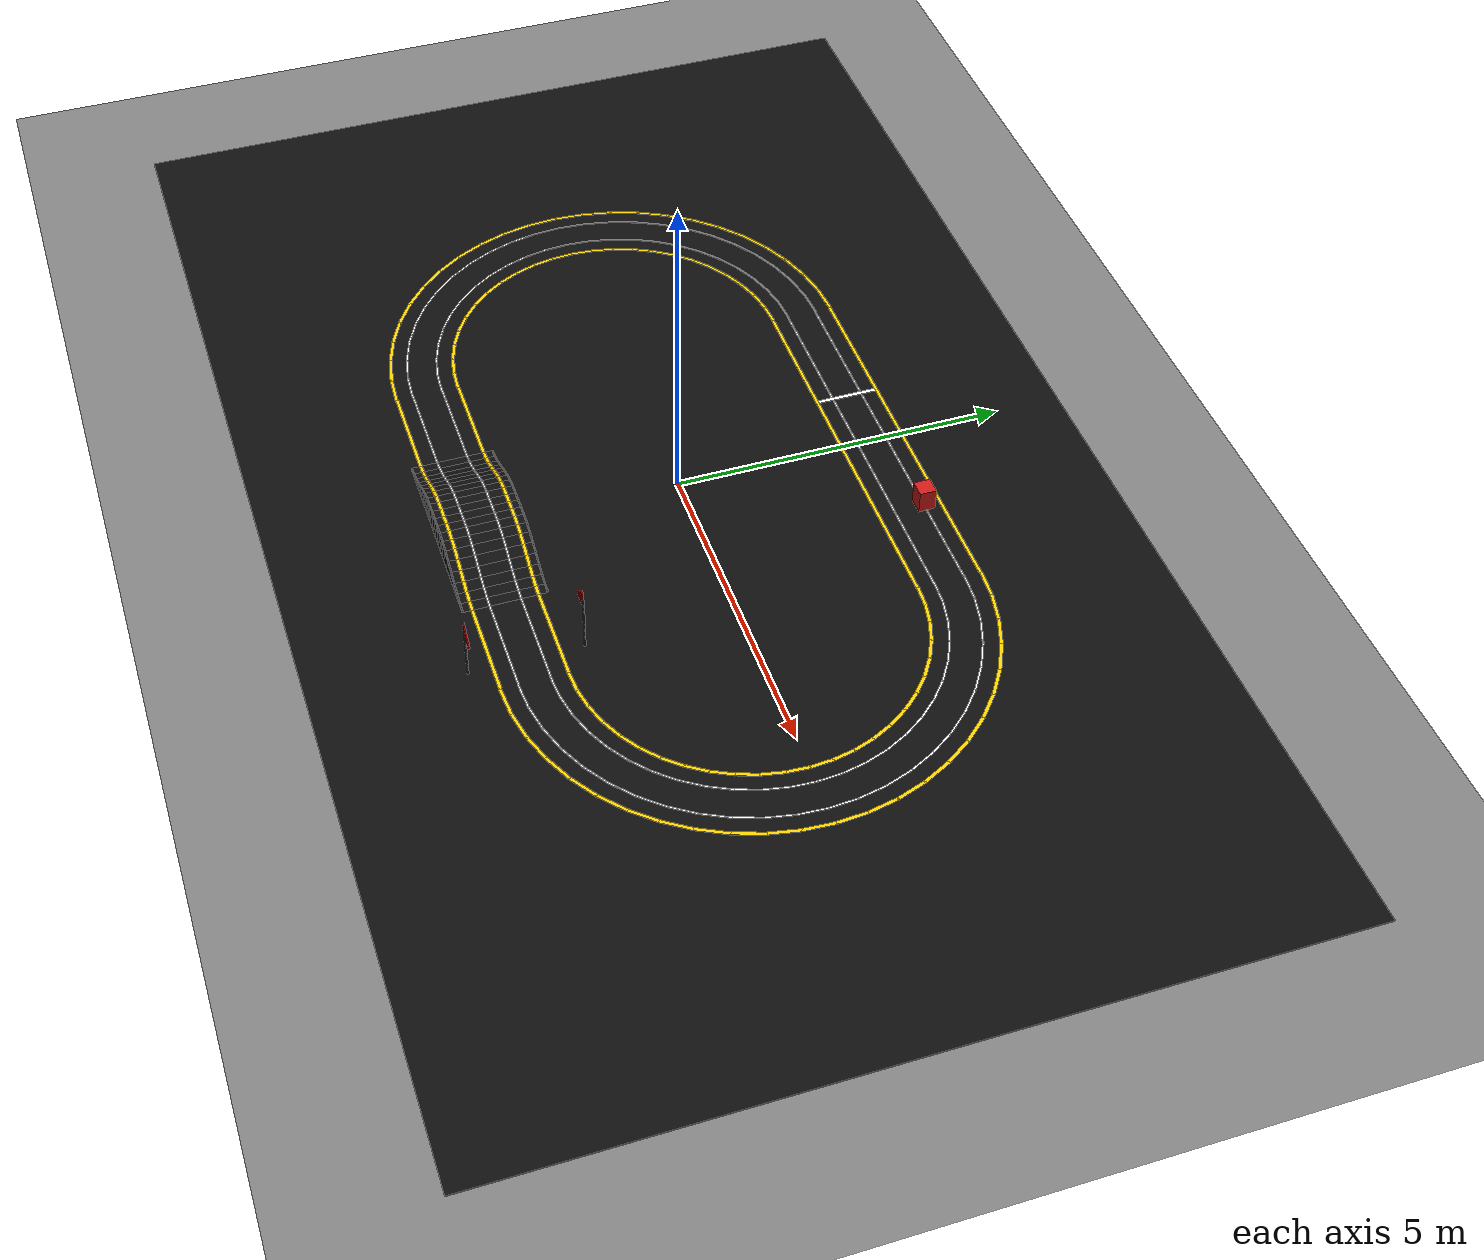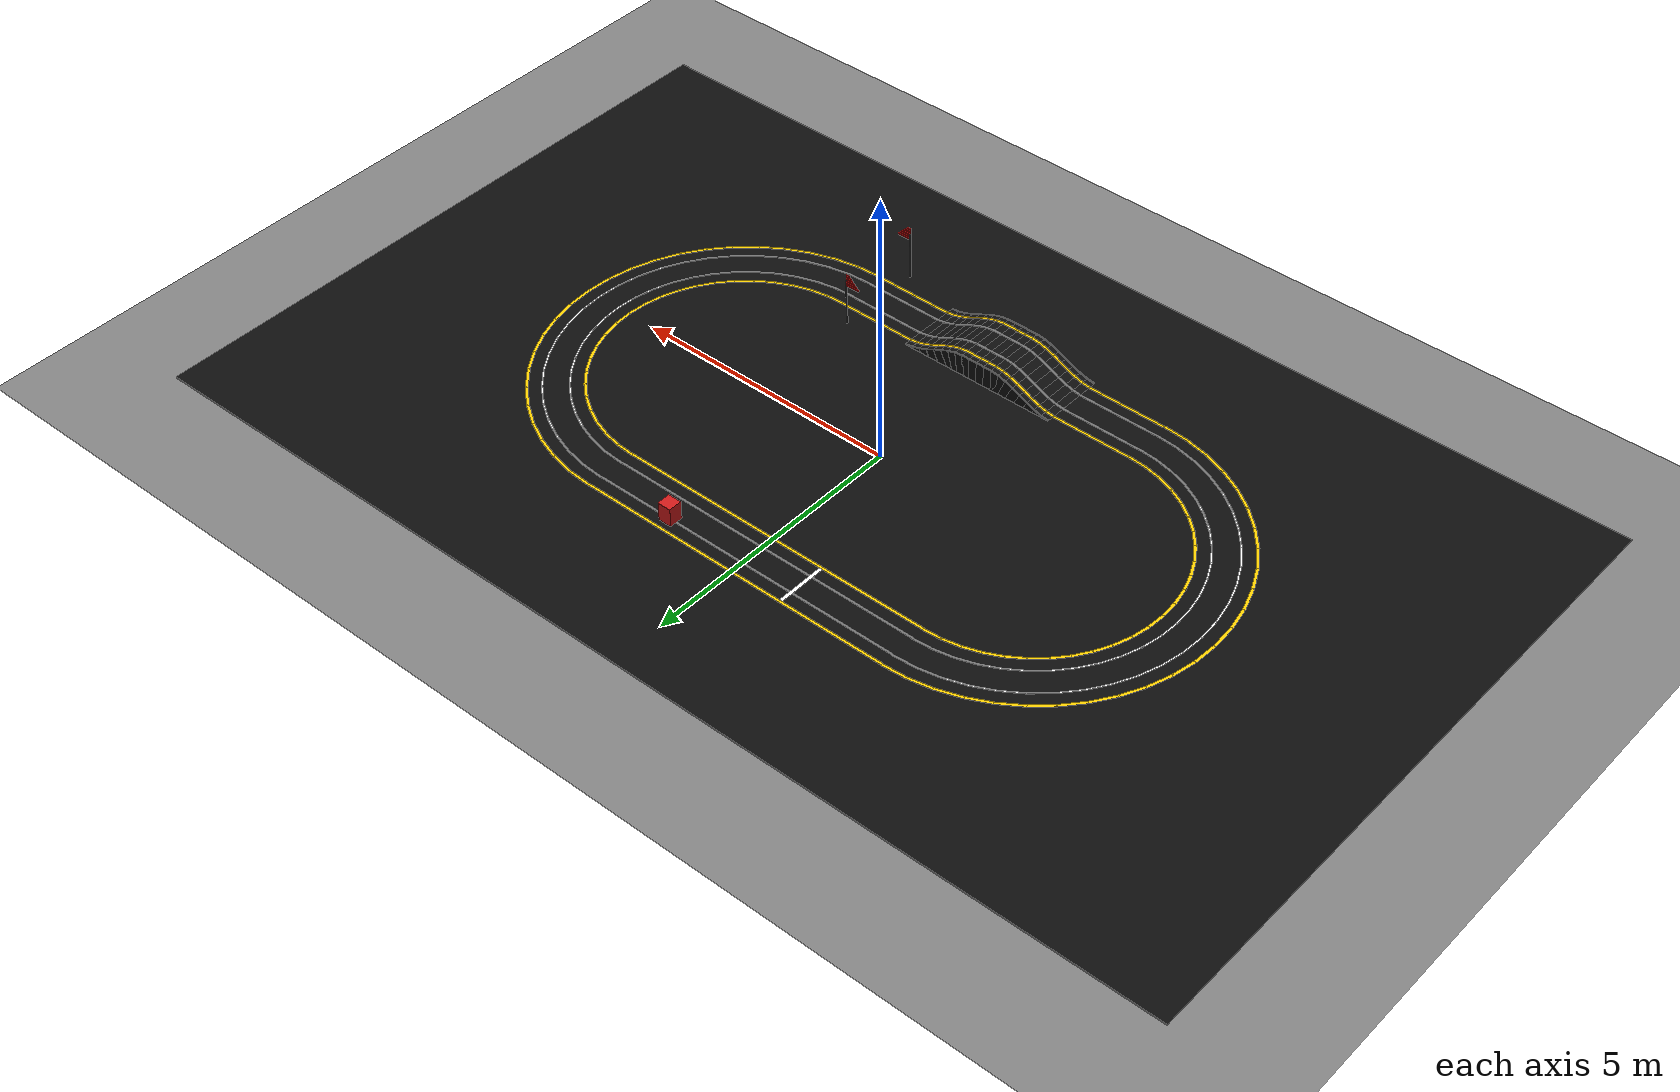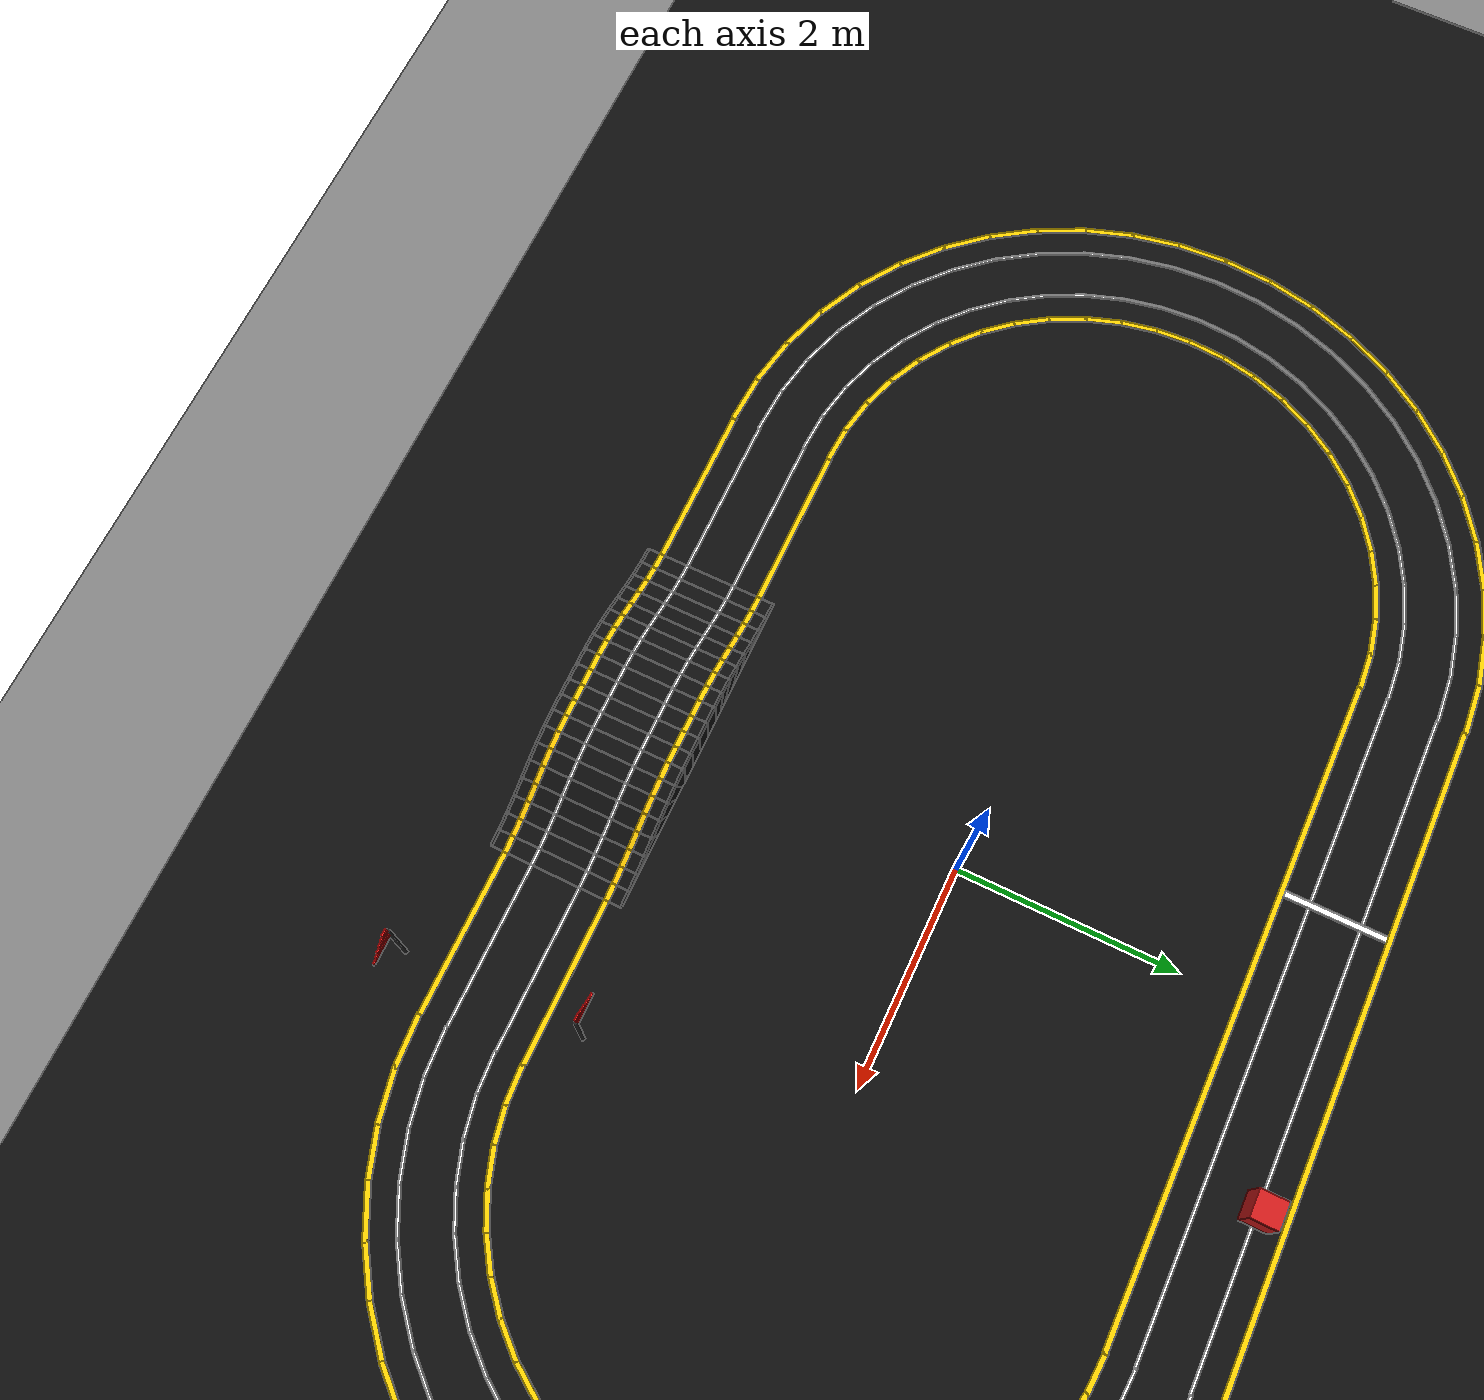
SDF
<?xml version="1.0" ?>
<sdf version="1.8">
  <world name="default">
      <plugin filename="gz-sim-physics-system" name="gz::sim::systems::Physics"/>
      <plugin filename="gz-sim-scene-broadcaster-system" name="gz::sim::systems::SceneBroadcaster"/>
      <plugin filename="gz-sim-sensors-system" name="gz::sim::systems::Sensors">
        <render_engine>ogre2</render_engine>
      </plugin>
      <plugin filename="gz-sim-user-commands-system" name="gz::sim::systems::UserCommands"/>

    <light type="directional" name="sun">
      <cast_shadows>true</cast_shadows>
      <pose>0 0 10 0 0 0</pose>
      <diffuse>1 1 1 1</diffuse>
      <specular>0.5 0.5 0.5 1</specular>
      <direction>-0.5 0.1 -0.9</direction>
    </light>

    <model name="ground_plane">
      <static>true</static>
      <link name="link">
        <visual name="visual">
          <geometry><plane><normal>0 0 1</normal><size>100 100</size></plane></geometry>
          <material>
            <ambient>0.5 0.5 0.5 1</ambient>
            <diffuse>0.5 0.5 0.5 1</diffuse>
          </material>
        </visual>
      </link>
    </model>

    <model name="race_track">
      <static>true</static>
      <link name="track_link">

        <visual name="asphalt_vis">
          <pose>0 0 0.01 0 0 0</pose>
          <geometry><box><size>20 12 0.02</size></box></geometry>
          <material>
            <ambient>0.05 0.05 0.05 1</ambient>
            <diffuse>0.05 0.05 0.05 1</diffuse>
          </material>
        </visual>
        <collision name="asphalt_col">
          <pose>0 0 0.01 0 0 0</pose>
          <geometry><box><size>20 12 0.02</size></box></geometry>
        </collision>

        <visual name="yel_out_top">
          <pose>0 3.475 0.022 0 0 0</pose>
          <geometry><box><size>6.0 0.05 0.002</size></box></geometry>
          <material>
            <ambient>1.0 0.8 0.0 1</ambient>
            <diffuse>1.0 0.8 0.0 1</diffuse>
          </material>
        </visual>
        <visual name="yel_out_bot">
          <pose>0 -3.475 0.022 0 0 0</pose>
          <geometry><box><size>6.0 0.05 0.002</size></box></geometry>
          <material>
            <ambient>1.0 0.8 0.0 1</ambient>
            <diffuse>1.0 0.8 0.0 1</diffuse>
          </material>
        </visual>
        <visual name="yel_out_lcurve_0">
          <pose>-3.2272758740747465 3.467559758254147 0.022 0 0 3.2070425005395804</pose>
          <geometry><box><size>0.4776202581160732 0.05 0.002</size></box></geometry>
          <material>
            <ambient>1.0 0.8 0.0 1</ambient>
            <diffuse>1.0 0.8 0.0 1</diffuse>
          </material>
        </visual>
        <visual name="yel_out_rcurve_0">
          <pose>3.227275874074747 -3.467559758254147 0.022 0 0 0.06544984694978728</pose>
          <geometry><box><size>0.4776202581160732 0.05 0.002</size></box></geometry>
          <material>
            <ambient>1.0 0.8 0.0 1</ambient>
            <diffuse>1.0 0.8 0.0 1</diffuse>
          </material>
        </visual>
        <visual name="yel_out_lcurve_1">
          <pose>-3.6779388690060455 3.4082288494012256 0.022 0 0 3.3379421944391554</pose>
          <geometry><box><size>0.4776202581160732 0.05 0.002</size></box></geometry>
          <material>
            <ambient>1.0 0.8 0.0 1</ambient>
            <diffuse>1.0 0.8 0.0 1</diffuse>
          </material>
        </visual>
        <visual name="yel_out_rcurve_1">
          <pose>3.677938869006046 -3.4082288494012256 0.022 0 0 0.19634954084936207</pose>
          <geometry><box><size>0.4776202581160732 0.05 0.002</size></box></geometry>
          <material>
            <ambient>1.0 0.8 0.0 1</ambient>
            <diffuse>1.0 0.8 0.0 1</diffuse>
          </material>
        </visual>
        <visual name="yel_out_lcurve_2">
          <pose>-4.117002141928486 3.2905821999954923 0.022 0 0 3.46884188833873</pose>
          <geometry><box><size>0.4776202581160732 0.05 0.002</size></box></geometry>
          <material>
            <ambient>1.0 0.8 0.0 1</ambient>
            <diffuse>1.0 0.8 0.0 1</diffuse>
          </material>
        </visual>
        <visual name="yel_out_rcurve_2">
          <pose>4.117002141928487 -3.290582199995492 0.022 0 0 0.32724923474893686</pose>
          <geometry><box><size>0.4776202581160732 0.05 0.002</size></box></geometry>
          <material>
            <ambient>1.0 0.8 0.0 1</ambient>
            <diffuse>1.0 0.8 0.0 1</diffuse>
          </material>
        </visual>
        <visual name="yel_out_lcurve_3">
          <pose>-4.5369531985110285 3.116632776826092 0.022 0 0 3.5997415822383045</pose>
          <geometry><box><size>0.4776202581160732 0.05 0.002</size></box></geometry>
          <material>
            <ambient>1.0 0.8 0.0 1</ambient>
            <diffuse>1.0 0.8 0.0 1</diffuse>
          </material>
        </visual>
        <visual name="yel_out_rcurve_3">
          <pose>4.536953198511029 -3.116632776826092 0.022 0 0 0.4581489286485114</pose>
          <geometry><box><size>0.4776202581160732 0.05 0.002</size></box></geometry>
          <material>
            <ambient>1.0 0.8 0.0 1</ambient>
            <diffuse>1.0 0.8 0.0 1</diffuse>
          </material>
        </visual>
        <visual name="yel_out_lcurve_4">
          <pose>-4.930606559743117 2.8893569027513455 0.022 0 0 3.730641276137879</pose>
          <geometry><box><size>0.4776202581160732 0.05 0.002</size></box></geometry>
          <material>
            <ambient>1.0 0.8 0.0 1</ambient>
            <diffuse>1.0 0.8 0.0 1</diffuse>
          </material>
        </visual>
        <visual name="yel_out_rcurve_4">
          <pose>4.930606559743118 -2.8893569027513446 0.022 0 0 0.5890486225480861</pose>
          <geometry><box><size>0.4776202581160732 0.05 0.002</size></box></geometry>
          <material>
            <ambient>1.0 0.8 0.0 1</ambient>
            <diffuse>1.0 0.8 0.0 1</diffuse>
          </material>
        </visual>
        <visual name="yel_out_lcurve_5">
          <pose>-5.29122670747274 2.6126433309894463 0.022 0 0 3.861540970037454</pose>
          <geometry><box><size>0.4776202581160732 0.05 0.002</size></box></geometry>
          <material>
            <ambient>1.0 0.8 0.0 1</ambient>
            <diffuse>1.0 0.8 0.0 1</diffuse>
          </material>
        </visual>
        <visual name="yel_out_rcurve_5">
          <pose>5.29122670747274 -2.6126433309894463 0.022 0 0 0.7199483164476609</pose>
          <geometry><box><size>0.4776202581160732 0.05 0.002</size></box></geometry>
          <material>
            <ambient>1.0 0.8 0.0 1</ambient>
            <diffuse>1.0 0.8 0.0 1</diffuse>
          </material>
        </visual>
        <visual name="yel_out_lcurve_6">
          <pose>-5.612643330989446 2.2912267074727395 0.022 0 0 3.9924406639370287</pose>
          <geometry><box><size>0.4776202581160732 0.05 0.002</size></box></geometry>
          <material>
            <ambient>1.0 0.8 0.0 1</ambient>
            <diffuse>1.0 0.8 0.0 1</diffuse>
          </material>
        </visual>
        <visual name="yel_out_rcurve_6">
          <pose>5.612643330989446 -2.2912267074727395 0.022 0 0 0.8508480103472356</pose>
          <geometry><box><size>0.4776202581160732 0.05 0.002</size></box></geometry>
          <material>
            <ambient>1.0 0.8 0.0 1</ambient>
            <diffuse>1.0 0.8 0.0 1</diffuse>
          </material>
        </visual>
        <visual name="yel_out_lcurve_7">
          <pose>-5.889356902751344 1.9306065597431188 0.022 0 0 4.123340357836604</pose>
          <geometry><box><size>0.4776202581160732 0.05 0.002</size></box></geometry>
          <material>
            <ambient>1.0 0.8 0.0 1</ambient>
            <diffuse>1.0 0.8 0.0 1</diffuse>
          </material>
        </visual>
        <visual name="yel_out_rcurve_7">
          <pose>5.889356902751345 -1.9306065597431177 0.022 0 0 0.9817477042468103</pose>
          <geometry><box><size>0.4776202581160732 0.05 0.002</size></box></geometry>
          <material>
            <ambient>1.0 0.8 0.0 1</ambient>
            <diffuse>1.0 0.8 0.0 1</diffuse>
          </material>
        </visual>
        <visual name="yel_out_lcurve_8">
          <pose>-6.116632776826092 1.5369531985110296 0.022 0 0 4.254240051736178</pose>
          <geometry><box><size>0.4776202581160732 0.05 0.002</size></box></geometry>
          <material>
            <ambient>1.0 0.8 0.0 1</ambient>
            <diffuse>1.0 0.8 0.0 1</diffuse>
          </material>
        </visual>
        <visual name="yel_out_rcurve_8">
          <pose>6.116632776826092 -1.5369531985110296 0.022 0 0 1.1126473981463851</pose>
          <geometry><box><size>0.4776202581160732 0.05 0.002</size></box></geometry>
          <material>
            <ambient>1.0 0.8 0.0 1</ambient>
            <diffuse>1.0 0.8 0.0 1</diffuse>
          </material>
        </visual>
        <visual name="yel_out_lcurve_9">
          <pose>-6.290582199995492 1.117002141928487 0.022 0 0 4.385139745635753</pose>
          <geometry><box><size>0.4776202581160732 0.05 0.002</size></box></geometry>
          <material>
            <ambient>1.0 0.8 0.0 1</ambient>
            <diffuse>1.0 0.8 0.0 1</diffuse>
          </material>
        </visual>
        <visual name="yel_out_rcurve_9">
          <pose>6.290582199995493 -1.1170021419284868 0.022 0 0 1.2435470920459597</pose>
          <geometry><box><size>0.4776202581160732 0.05 0.002</size></box></geometry>
          <material>
            <ambient>1.0 0.8 0.0 1</ambient>
            <diffuse>1.0 0.8 0.0 1</diffuse>
          </material>
        </visual>
        <visual name="yel_out_lcurve_10">
          <pose>-6.408228849401226 0.6779388690060469 0.022 0 0 4.516039439535327</pose>
          <geometry><box><size>0.4776202581160732 0.05 0.002</size></box></geometry>
          <material>
            <ambient>1.0 0.8 0.0 1</ambient>
            <diffuse>1.0 0.8 0.0 1</diffuse>
          </material>
        </visual>
        <visual name="yel_out_rcurve_10">
          <pose>6.408228849401226 -0.677938869006046 0.022 0 0 1.3744467859455343</pose>
          <geometry><box><size>0.4776202581160732 0.05 0.002</size></box></geometry>
          <material>
            <ambient>1.0 0.8 0.0 1</ambient>
            <diffuse>1.0 0.8 0.0 1</diffuse>
          </material>
        </visual>
        <visual name="yel_out_lcurve_11">
          <pose>-6.467559758254147 0.22727587407474734 0.022 0 0 4.646939133434902</pose>
          <geometry><box><size>0.4776202581160732 0.05 0.002</size></box></geometry>
          <material>
            <ambient>1.0 0.8 0.0 1</ambient>
            <diffuse>1.0 0.8 0.0 1</diffuse>
          </material>
        </visual>
        <visual name="yel_out_rcurve_11">
          <pose>6.467559758254147 -0.22727587407474728 0.022 0 0 1.5053464798451093</pose>
          <geometry><box><size>0.4776202581160732 0.05 0.002</size></box></geometry>
          <material>
            <ambient>1.0 0.8 0.0 1</ambient>
            <diffuse>1.0 0.8 0.0 1</diffuse>
          </material>
        </visual>
        <visual name="yel_out_lcurve_12">
          <pose>-6.467559758254147 -0.22727587407474648 0.022 0 0 4.777838827334477</pose>
          <geometry><box><size>0.4776202581160732 0.05 0.002</size></box></geometry>
          <material>
            <ambient>1.0 0.8 0.0 1</ambient>
            <diffuse>1.0 0.8 0.0 1</diffuse>
          </material>
        </visual>
        <visual name="yel_out_rcurve_12">
          <pose>6.467559758254147 0.2272758740747469 0.022 0 0 1.6362461737446838</pose>
          <geometry><box><size>0.4776202581160732 0.05 0.002</size></box></geometry>
          <material>
            <ambient>1.0 0.8 0.0 1</ambient>
            <diffuse>1.0 0.8 0.0 1</diffuse>
          </material>
        </visual>
        <visual name="yel_out_lcurve_13">
          <pose>-6.408228849401226 -0.6779388690060445 0.022 0 0 4.908738521234051</pose>
          <geometry><box><size>0.4776202581160732 0.05 0.002</size></box></geometry>
          <material>
            <ambient>1.0 0.8 0.0 1</ambient>
            <diffuse>1.0 0.8 0.0 1</diffuse>
          </material>
        </visual>
        <visual name="yel_out_rcurve_13">
          <pose>6.408228849401226 0.6779388690060454 0.022 0 0 1.7671458676442584</pose>
          <geometry><box><size>0.4776202581160732 0.05 0.002</size></box></geometry>
          <material>
            <ambient>1.0 0.8 0.0 1</ambient>
            <diffuse>1.0 0.8 0.0 1</diffuse>
          </material>
        </visual>
        <visual name="yel_out_lcurve_14">
          <pose>-6.290582199995493 -1.1170021419284848 0.022 0 0 5.0396382151336265</pose>
          <geometry><box><size>0.4776202581160732 0.05 0.002</size></box></geometry>
          <material>
            <ambient>1.0 0.8 0.0 1</ambient>
            <diffuse>1.0 0.8 0.0 1</diffuse>
          </material>
        </visual>
        <visual name="yel_out_rcurve_14">
          <pose>6.290582199995493 1.117002141928486 0.022 0 0 1.8980455615438332</pose>
          <geometry><box><size>0.4776202581160732 0.05 0.002</size></box></geometry>
          <material>
            <ambient>1.0 0.8 0.0 1</ambient>
            <diffuse>1.0 0.8 0.0 1</diffuse>
          </material>
        </visual>
        <visual name="yel_out_lcurve_15">
          <pose>-6.116632776826092 -1.5369531985110287 0.022 0 0 5.170537909033201</pose>
          <geometry><box><size>0.4776202581160732 0.05 0.002</size></box></geometry>
          <material>
            <ambient>1.0 0.8 0.0 1</ambient>
            <diffuse>1.0 0.8 0.0 1</diffuse>
          </material>
        </visual>
        <visual name="yel_out_rcurve_15">
          <pose>6.116632776826092 1.5369531985110287 0.022 0 0 2.028945255443408</pose>
          <geometry><box><size>0.4776202581160732 0.05 0.002</size></box></geometry>
          <material>
            <ambient>1.0 0.8 0.0 1</ambient>
            <diffuse>1.0 0.8 0.0 1</diffuse>
          </material>
        </visual>
        <visual name="yel_out_lcurve_16">
          <pose>-5.889356902751345 -1.9306065597431168 0.022 0 0 5.301437602932776</pose>
          <geometry><box><size>0.4776202581160732 0.05 0.002</size></box></geometry>
          <material>
            <ambient>1.0 0.8 0.0 1</ambient>
            <diffuse>1.0 0.8 0.0 1</diffuse>
          </material>
        </visual>
        <visual name="yel_out_rcurve_16">
          <pose>5.889356902751345 1.9306065597431172 0.022 0 0 2.1598449493429825</pose>
          <geometry><box><size>0.4776202581160732 0.05 0.002</size></box></geometry>
          <material>
            <ambient>1.0 0.8 0.0 1</ambient>
            <diffuse>1.0 0.8 0.0 1</diffuse>
          </material>
        </visual>
        <visual name="yel_out_lcurve_17">
          <pose>-5.612643330989448 -2.291226707472738 0.022 0 0 5.43233729683235</pose>
          <geometry><box><size>0.4776202581160732 0.05 0.002</size></box></geometry>
          <material>
            <ambient>1.0 0.8 0.0 1</ambient>
            <diffuse>1.0 0.8 0.0 1</diffuse>
          </material>
        </visual>
        <visual name="yel_out_rcurve_17">
          <pose>5.612643330989447 2.291226707472739 0.022 0 0 2.290744643242557</pose>
          <geometry><box><size>0.4776202581160732 0.05 0.002</size></box></geometry>
          <material>
            <ambient>1.0 0.8 0.0 1</ambient>
            <diffuse>1.0 0.8 0.0 1</diffuse>
          </material>
        </visual>
        <visual name="yel_out_lcurve_18">
          <pose>-5.29122670747274 -2.612643330989446 0.022 0 0 5.563236990731925</pose>
          <geometry><box><size>0.4776202581160732 0.05 0.002</size></box></geometry>
          <material>
            <ambient>1.0 0.8 0.0 1</ambient>
            <diffuse>1.0 0.8 0.0 1</diffuse>
          </material>
        </visual>
        <visual name="yel_out_rcurve_18">
          <pose>5.29122670747274 2.612643330989446 0.022 0 0 2.421644337142132</pose>
          <geometry><box><size>0.4776202581160732 0.05 0.002</size></box></geometry>
          <material>
            <ambient>1.0 0.8 0.0 1</ambient>
            <diffuse>1.0 0.8 0.0 1</diffuse>
          </material>
        </visual>
        <visual name="yel_out_lcurve_19">
          <pose>-4.930606559743118 -2.8893569027513446 0.022 0 0 5.6941366846315</pose>
          <geometry><box><size>0.4776202581160732 0.05 0.002</size></box></geometry>
          <material>
            <ambient>1.0 0.8 0.0 1</ambient>
            <diffuse>1.0 0.8 0.0 1</diffuse>
          </material>
        </visual>
        <visual name="yel_out_rcurve_19">
          <pose>4.930606559743119 2.8893569027513446 0.022 0 0 2.5525440310417067</pose>
          <geometry><box><size>0.4776202581160732 0.05 0.002</size></box></geometry>
          <material>
            <ambient>1.0 0.8 0.0 1</ambient>
            <diffuse>1.0 0.8 0.0 1</diffuse>
          </material>
        </visual>
        <visual name="yel_out_lcurve_20">
          <pose>-4.536953198511032 -3.1166327768260906 0.022 0 0 5.825036378531074</pose>
          <geometry><box><size>0.4776202581160732 0.05 0.002</size></box></geometry>
          <material>
            <ambient>1.0 0.8 0.0 1</ambient>
            <diffuse>1.0 0.8 0.0 1</diffuse>
          </material>
        </visual>
        <visual name="yel_out_rcurve_20">
          <pose>4.53695319851103 3.116632776826092 0.022 0 0 2.6834437249412817</pose>
          <geometry><box><size>0.4776202581160732 0.05 0.002</size></box></geometry>
          <material>
            <ambient>1.0 0.8 0.0 1</ambient>
            <diffuse>1.0 0.8 0.0 1</diffuse>
          </material>
        </visual>
        <visual name="yel_out_lcurve_21">
          <pose>-4.117002141928487 -3.290582199995492 0.022 0 0 5.955936072430649</pose>
          <geometry><box><size>0.4776202581160732 0.05 0.002</size></box></geometry>
          <material>
            <ambient>1.0 0.8 0.0 1</ambient>
            <diffuse>1.0 0.8 0.0 1</diffuse>
          </material>
        </visual>
        <visual name="yel_out_rcurve_21">
          <pose>4.117002141928487 3.290582199995492 0.022 0 0 2.8143434188408563</pose>
          <geometry><box><size>0.4776202581160732 0.05 0.002</size></box></geometry>
          <material>
            <ambient>1.0 0.8 0.0 1</ambient>
            <diffuse>1.0 0.8 0.0 1</diffuse>
          </material>
        </visual>
        <visual name="yel_out_lcurve_22">
          <pose>-3.6779388690060473 -3.4082288494012256 0.022 0 0 6.086835766330224</pose>
          <geometry><box><size>0.4776202581160732 0.05 0.002</size></box></geometry>
          <material>
            <ambient>1.0 0.8 0.0 1</ambient>
            <diffuse>1.0 0.8 0.0 1</diffuse>
          </material>
        </visual>
        <visual name="yel_out_rcurve_22">
          <pose>3.677938869006047 3.4082288494012256 0.022 0 0 2.945243112740431</pose>
          <geometry><box><size>0.4776202581160732 0.05 0.002</size></box></geometry>
          <material>
            <ambient>1.0 0.8 0.0 1</ambient>
            <diffuse>1.0 0.8 0.0 1</diffuse>
          </material>
        </visual>
        <visual name="yel_out_lcurve_23">
          <pose>-3.227275874074749 -3.467559758254147 0.022 0 0 6.2177354602297985</pose>
          <geometry><box><size>0.4776202581160732 0.05 0.002</size></box></geometry>
          <material>
            <ambient>1.0 0.8 0.0 1</ambient>
            <diffuse>1.0 0.8 0.0 1</diffuse>
          </material>
        </visual>
        <visual name="yel_out_rcurve_23">
          <pose>3.227275874074748 3.467559758254147 0.022 0 0 3.0761428066400054</pose>
          <geometry><box><size>0.4776202581160732 0.05 0.002</size></box></geometry>
          <material>
            <ambient>1.0 0.8 0.0 1</ambient>
            <diffuse>1.0 0.8 0.0 1</diffuse>
          </material>
        </visual>
        <visual name="whi_out_top">
          <pose>0 3.225 0.022 0 0 0</pose>
          <geometry><box><size>6.0 0.025 0.002</size></box></geometry>
          <material>
            <ambient>1.0 1.0 1.0 1</ambient>
            <diffuse>1.0 1.0 1.0 1</diffuse>
          </material>
        </visual>
        <visual name="whi_out_bot">
          <pose>0 -3.225 0.022 0 0 0</pose>
          <geometry><box><size>6.0 0.025 0.002</size></box></geometry>
          <material>
            <ambient>1.0 1.0 1.0 1</ambient>
            <diffuse>1.0 1.0 1.0 1</diffuse>
          </material>
        </visual>
        <visual name="whi_out_lcurve_0">
          <pose>-3.2109250917672107 3.2180950274444964 0.022 0 0 3.2070425005395804</pose>
          <geometry><box><size>0.4432590884674349 0.025 0.002</size></box></geometry>
          <material>
            <ambient>1.0 1.0 1.0 1</ambient>
            <diffuse>1.0 1.0 1.0 1</diffuse>
          </material>
        </visual>
        <visual name="whi_out_rcurve_0">
          <pose>3.210925091767211 -3.2180950274444964 0.022 0 0 0.06544984694978728</pose>
          <geometry><box><size>0.4432590884674349 0.025 0.002</size></box></geometry>
          <material>
            <ambient>1.0 1.0 1.0 1</ambient>
            <diffuse>1.0 1.0 1.0 1</diffuse>
          </material>
        </visual>
        <visual name="whi_out_lcurve_1">
          <pose>-3.6291662885020135 3.163032529300418 0.022 0 0 3.3379421944391554</pose>
          <geometry><box><size>0.4432590884674349 0.025 0.002</size></box></geometry>
          <material>
            <ambient>1.0 1.0 1.0 1</ambient>
            <diffuse>1.0 1.0 1.0 1</diffuse>
          </material>
        </visual>
        <visual name="whi_out_rcurve_1">
          <pose>3.629166288502014 -3.163032529300418 0.022 0 0 0.19634954084936207</pose>
          <geometry><box><size>0.4432590884674349 0.025 0.002</size></box></geometry>
          <material>
            <ambient>1.0 1.0 1.0 1</ambient>
            <diffuse>1.0 1.0 1.0 1</diffuse>
          </material>
        </visual>
        <visual name="whi_out_lcurve_2">
          <pose>-4.036642275602696 3.0538496676217157 0.022 0 0 3.46884188833873</pose>
          <geometry><box><size>0.4432590884674349 0.025 0.002</size></box></geometry>
          <material>
            <ambient>1.0 1.0 1.0 1</ambient>
            <diffuse>1.0 1.0 1.0 1</diffuse>
          </material>
        </visual>
        <visual name="whi_out_rcurve_2">
          <pose>4.036642275602697 -3.0538496676217157 0.022 0 0 0.32724923474893686</pose>
          <geometry><box><size>0.4432590884674349 0.025 0.002</size></box></geometry>
          <material>
            <ambient>1.0 1.0 1.0 1</ambient>
            <diffuse>1.0 1.0 1.0 1</diffuse>
          </material>
        </visual>
        <visual name="whi_out_lcurve_3">
          <pose>-4.426381025956279 2.89241459144292 0.022 0 0 3.5997415822383045</pose>
          <geometry><box><size>0.4432590884674349 0.025 0.002</size></box></geometry>
          <material>
            <ambient>1.0 1.0 1.0 1</ambient>
            <diffuse>1.0 1.0 1.0 1</diffuse>
          </material>
        </visual>
        <visual name="whi_out_rcurve_3">
          <pose>4.426381025956279 -2.89241459144292 0.022 0 0 0.4581489286485114</pose>
          <geometry><box><size>0.4432590884674349 0.025 0.002</size></box></geometry>
          <material>
            <ambient>1.0 1.0 1.0 1</ambient>
            <diffuse>1.0 1.0 1.0 1</diffuse>
          </material>
        </visual>
        <visual name="whi_out_lcurve_4">
          <pose>-4.7917140014882165 2.6814894996757093 0.022 0 0 3.730641276137879</pose>
          <geometry><box><size>0.4432590884674349 0.025 0.002</size></box></geometry>
          <material>
            <ambient>1.0 1.0 1.0 1</ambient>
            <diffuse>1.0 1.0 1.0 1</diffuse>
          </material>
        </visual>
        <visual name="whi_out_rcurve_4">
          <pose>4.791714001488217 -2.6814894996757084 0.022 0 0 0.5890486225480861</pose>
          <geometry><box><size>0.4432590884674349 0.025 0.002</size></box></geometry>
          <material>
            <ambient>1.0 1.0 1.0 1</ambient>
            <diffuse>1.0 1.0 1.0 1</diffuse>
          </material>
        </visual>
        <visual name="whi_out_lcurve_5">
          <pose>-5.126390253697722 2.424683379119702 0.022 0 0 3.861540970037454</pose>
          <geometry><box><size>0.4432590884674349 0.025 0.002</size></box></geometry>
          <material>
            <ambient>1.0 1.0 1.0 1</ambient>
            <diffuse>1.0 1.0 1.0 1</diffuse>
          </material>
        </visual>
        <visual name="whi_out_rcurve_5">
          <pose>5.126390253697722 -2.424683379119702 0.022 0 0 0.7199483164476609</pose>
          <geometry><box><size>0.4432590884674349 0.025 0.002</size></box></geometry>
          <material>
            <ambient>1.0 1.0 1.0 1</ambient>
            <diffuse>1.0 1.0 1.0 1</diffuse>
          </material>
        </visual>
        <visual name="whi_out_lcurve_6">
          <pose>-5.424683379119702 2.1263902536977226 0.022 0 0 3.9924406639370287</pose>
          <geometry><box><size>0.4432590884674349 0.025 0.002</size></box></geometry>
          <material>
            <ambient>1.0 1.0 1.0 1</ambient>
            <diffuse>1.0 1.0 1.0 1</diffuse>
          </material>
        </visual>
        <visual name="whi_out_rcurve_6">
          <pose>5.424683379119703 -2.1263902536977226 0.022 0 0 0.8508480103472356</pose>
          <geometry><box><size>0.4432590884674349 0.025 0.002</size></box></geometry>
          <material>
            <ambient>1.0 1.0 1.0 1</ambient>
            <diffuse>1.0 1.0 1.0 1</diffuse>
          </material>
        </visual>
        <visual name="whi_out_lcurve_7">
          <pose>-5.681489499675708 1.7917140014882182 0.022 0 0 4.123340357836604</pose>
          <geometry><box><size>0.4432590884674349 0.025 0.002</size></box></geometry>
          <material>
            <ambient>1.0 1.0 1.0 1</ambient>
            <diffuse>1.0 1.0 1.0 1</diffuse>
          </material>
        </visual>
        <visual name="whi_out_rcurve_7">
          <pose>5.681489499675708 -1.7917140014882171 0.022 0 0 0.9817477042468103</pose>
          <geometry><box><size>0.4432590884674349 0.025 0.002</size></box></geometry>
          <material>
            <ambient>1.0 1.0 1.0 1</ambient>
            <diffuse>1.0 1.0 1.0 1</diffuse>
          </material>
        </visual>
        <visual name="whi_out_lcurve_8">
          <pose>-5.89241459144292 1.4263810259562792 0.022 0 0 4.254240051736178</pose>
          <geometry><box><size>0.4432590884674349 0.025 0.002</size></box></geometry>
          <material>
            <ambient>1.0 1.0 1.0 1</ambient>
            <diffuse>1.0 1.0 1.0 1</diffuse>
          </material>
        </visual>
        <visual name="whi_out_rcurve_8">
          <pose>5.89241459144292 -1.4263810259562792 0.022 0 0 1.1126473981463851</pose>
          <geometry><box><size>0.4432590884674349 0.025 0.002</size></box></geometry>
          <material>
            <ambient>1.0 1.0 1.0 1</ambient>
            <diffuse>1.0 1.0 1.0 1</diffuse>
          </material>
        </visual>
        <visual name="whi_out_lcurve_9">
          <pose>-6.053849667621716 1.0366422756026967 0.022 0 0 4.385139745635753</pose>
          <geometry><box><size>0.4432590884674349 0.025 0.002</size></box></geometry>
          <material>
            <ambient>1.0 1.0 1.0 1</ambient>
            <diffuse>1.0 1.0 1.0 1</diffuse>
          </material>
        </visual>
        <visual name="whi_out_rcurve_9">
          <pose>6.053849667621716 -1.0366422756026963 0.022 0 0 1.2435470920459597</pose>
          <geometry><box><size>0.4432590884674349 0.025 0.002</size></box></geometry>
          <material>
            <ambient>1.0 1.0 1.0 1</ambient>
            <diffuse>1.0 1.0 1.0 1</diffuse>
          </material>
        </visual>
        <visual name="whi_out_lcurve_10">
          <pose>-6.163032529300418 0.6291662885020147 0.022 0 0 4.516039439535327</pose>
          <geometry><box><size>0.4432590884674349 0.025 0.002</size></box></geometry>
          <material>
            <ambient>1.0 1.0 1.0 1</ambient>
            <diffuse>1.0 1.0 1.0 1</diffuse>
          </material>
        </visual>
        <visual name="whi_out_rcurve_10">
          <pose>6.163032529300418 -0.629166288502014 0.022 0 0 1.3744467859455343</pose>
          <geometry><box><size>0.4432590884674349 0.025 0.002</size></box></geometry>
          <material>
            <ambient>1.0 1.0 1.0 1</ambient>
            <diffuse>1.0 1.0 1.0 1</diffuse>
          </material>
        </visual>
        <visual name="whi_out_lcurve_11">
          <pose>-6.218095027444496 0.21092509176721155 0.022 0 0 4.646939133434902</pose>
          <geometry><box><size>0.4432590884674349 0.025 0.002</size></box></geometry>
          <material>
            <ambient>1.0 1.0 1.0 1</ambient>
            <diffuse>1.0 1.0 1.0 1</diffuse>
          </material>
        </visual>
        <visual name="whi_out_rcurve_11">
          <pose>6.218095027444496 -0.21092509176721153 0.022 0 0 1.5053464798451093</pose>
          <geometry><box><size>0.4432590884674349 0.025 0.002</size></box></geometry>
          <material>
            <ambient>1.0 1.0 1.0 1</ambient>
            <diffuse>1.0 1.0 1.0 1</diffuse>
          </material>
        </visual>
        <visual name="whi_out_lcurve_12">
          <pose>-6.218095027444496 -0.21092509176721075 0.022 0 0 4.777838827334477</pose>
          <geometry><box><size>0.4432590884674349 0.025 0.002</size></box></geometry>
          <material>
            <ambient>1.0 1.0 1.0 1</ambient>
            <diffuse>1.0 1.0 1.0 1</diffuse>
          </material>
        </visual>
        <visual name="whi_out_rcurve_12">
          <pose>6.218095027444496 0.21092509176721116 0.022 0 0 1.6362461737446838</pose>
          <geometry><box><size>0.4432590884674349 0.025 0.002</size></box></geometry>
          <material>
            <ambient>1.0 1.0 1.0 1</ambient>
            <diffuse>1.0 1.0 1.0 1</diffuse>
          </material>
        </visual>
        <visual name="whi_out_lcurve_13">
          <pose>-6.163032529300418 -0.6291662885020125 0.022 0 0 4.908738521234051</pose>
          <geometry><box><size>0.4432590884674349 0.025 0.002</size></box></geometry>
          <material>
            <ambient>1.0 1.0 1.0 1</ambient>
            <diffuse>1.0 1.0 1.0 1</diffuse>
          </material>
        </visual>
        <visual name="whi_out_rcurve_13">
          <pose>6.163032529300418 0.6291662885020134 0.022 0 0 1.7671458676442584</pose>
          <geometry><box><size>0.4432590884674349 0.025 0.002</size></box></geometry>
          <material>
            <ambient>1.0 1.0 1.0 1</ambient>
            <diffuse>1.0 1.0 1.0 1</diffuse>
          </material>
        </visual>
        <visual name="whi_out_lcurve_14">
          <pose>-6.053849667621716 -1.0366422756026945 0.022 0 0 5.0396382151336265</pose>
          <geometry><box><size>0.4432590884674349 0.025 0.002</size></box></geometry>
          <material>
            <ambient>1.0 1.0 1.0 1</ambient>
            <diffuse>1.0 1.0 1.0 1</diffuse>
          </material>
        </visual>
        <visual name="whi_out_rcurve_14">
          <pose>6.053849667621716 1.0366422756026956 0.022 0 0 1.8980455615438332</pose>
          <geometry><box><size>0.4432590884674349 0.025 0.002</size></box></geometry>
          <material>
            <ambient>1.0 1.0 1.0 1</ambient>
            <diffuse>1.0 1.0 1.0 1</diffuse>
          </material>
        </visual>
        <visual name="whi_out_lcurve_15">
          <pose>-5.89241459144292 -1.4263810259562786 0.022 0 0 5.170537909033201</pose>
          <geometry><box><size>0.4432590884674349 0.025 0.002</size></box></geometry>
          <material>
            <ambient>1.0 1.0 1.0 1</ambient>
            <diffuse>1.0 1.0 1.0 1</diffuse>
          </material>
        </visual>
        <visual name="whi_out_rcurve_15">
          <pose>5.89241459144292 1.4263810259562786 0.022 0 0 2.028945255443408</pose>
          <geometry><box><size>0.4432590884674349 0.025 0.002</size></box></geometry>
          <material>
            <ambient>1.0 1.0 1.0 1</ambient>
            <diffuse>1.0 1.0 1.0 1</diffuse>
          </material>
        </visual>
        <visual name="whi_out_lcurve_16">
          <pose>-5.68148949967571 -1.7917140014882162 0.022 0 0 5.301437602932776</pose>
          <geometry><box><size>0.4432590884674349 0.025 0.002</size></box></geometry>
          <material>
            <ambient>1.0 1.0 1.0 1</ambient>
            <diffuse>1.0 1.0 1.0 1</diffuse>
          </material>
        </visual>
        <visual name="whi_out_rcurve_16">
          <pose>5.681489499675709 1.7917140014882167 0.022 0 0 2.1598449493429825</pose>
          <geometry><box><size>0.4432590884674349 0.025 0.002</size></box></geometry>
          <material>
            <ambient>1.0 1.0 1.0 1</ambient>
            <diffuse>1.0 1.0 1.0 1</diffuse>
          </material>
        </visual>
        <visual name="whi_out_lcurve_17">
          <pose>-5.424683379119703 -2.126390253697721 0.022 0 0 5.43233729683235</pose>
          <geometry><box><size>0.4432590884674349 0.025 0.002</size></box></geometry>
          <material>
            <ambient>1.0 1.0 1.0 1</ambient>
            <diffuse>1.0 1.0 1.0 1</diffuse>
          </material>
        </visual>
        <visual name="whi_out_rcurve_17">
          <pose>5.424683379119703 2.1263902536977217 0.022 0 0 2.290744643242557</pose>
          <geometry><box><size>0.4432590884674349 0.025 0.002</size></box></geometry>
          <material>
            <ambient>1.0 1.0 1.0 1</ambient>
            <diffuse>1.0 1.0 1.0 1</diffuse>
          </material>
        </visual>
        <visual name="whi_out_lcurve_18">
          <pose>-5.126390253697723 -2.4246833791197018 0.022 0 0 5.563236990731925</pose>
          <geometry><box><size>0.4432590884674349 0.025 0.002</size></box></geometry>
          <material>
            <ambient>1.0 1.0 1.0 1</ambient>
            <diffuse>1.0 1.0 1.0 1</diffuse>
          </material>
        </visual>
        <visual name="whi_out_rcurve_18">
          <pose>5.126390253697723 2.4246833791197018 0.022 0 0 2.421644337142132</pose>
          <geometry><box><size>0.4432590884674349 0.025 0.002</size></box></geometry>
          <material>
            <ambient>1.0 1.0 1.0 1</ambient>
            <diffuse>1.0 1.0 1.0 1</diffuse>
          </material>
        </visual>
        <visual name="whi_out_lcurve_19">
          <pose>-4.791714001488217 -2.6814894996757084 0.022 0 0 5.6941366846315</pose>
          <geometry><box><size>0.4432590884674349 0.025 0.002</size></box></geometry>
          <material>
            <ambient>1.0 1.0 1.0 1</ambient>
            <diffuse>1.0 1.0 1.0 1</diffuse>
          </material>
        </visual>
        <visual name="whi_out_rcurve_19">
          <pose>4.791714001488218 2.681489499675708 0.022 0 0 2.5525440310417067</pose>
          <geometry><box><size>0.4432590884674349 0.025 0.002</size></box></geometry>
          <material>
            <ambient>1.0 1.0 1.0 1</ambient>
            <diffuse>1.0 1.0 1.0 1</diffuse>
          </material>
        </visual>
        <visual name="whi_out_lcurve_20">
          <pose>-4.426381025956282 -2.8924145914429187 0.022 0 0 5.825036378531074</pose>
          <geometry><box><size>0.4432590884674349 0.025 0.002</size></box></geometry>
          <material>
            <ambient>1.0 1.0 1.0 1</ambient>
            <diffuse>1.0 1.0 1.0 1</diffuse>
          </material>
        </visual>
        <visual name="whi_out_rcurve_20">
          <pose>4.42638102595628 2.8924145914429196 0.022 0 0 2.6834437249412817</pose>
          <geometry><box><size>0.4432590884674349 0.025 0.002</size></box></geometry>
          <material>
            <ambient>1.0 1.0 1.0 1</ambient>
            <diffuse>1.0 1.0 1.0 1</diffuse>
          </material>
        </visual>
        <visual name="whi_out_lcurve_21">
          <pose>-4.036642275602697 -3.0538496676217157 0.022 0 0 5.955936072430649</pose>
          <geometry><box><size>0.4432590884674349 0.025 0.002</size></box></geometry>
          <material>
            <ambient>1.0 1.0 1.0 1</ambient>
            <diffuse>1.0 1.0 1.0 1</diffuse>
          </material>
        </visual>
        <visual name="whi_out_rcurve_21">
          <pose>4.036642275602697 3.0538496676217157 0.022 0 0 2.8143434188408563</pose>
          <geometry><box><size>0.4432590884674349 0.025 0.002</size></box></geometry>
          <material>
            <ambient>1.0 1.0 1.0 1</ambient>
            <diffuse>1.0 1.0 1.0 1</diffuse>
          </material>
        </visual>
        <visual name="whi_out_lcurve_22">
          <pose>-3.629166288502015 -3.163032529300418 0.022 0 0 6.086835766330224</pose>
          <geometry><box><size>0.4432590884674349 0.025 0.002</size></box></geometry>
          <material>
            <ambient>1.0 1.0 1.0 1</ambient>
            <diffuse>1.0 1.0 1.0 1</diffuse>
          </material>
        </visual>
        <visual name="whi_out_rcurve_22">
          <pose>3.6291662885020144 3.163032529300418 0.022 0 0 2.945243112740431</pose>
          <geometry><box><size>0.4432590884674349 0.025 0.002</size></box></geometry>
          <material>
            <ambient>1.0 1.0 1.0 1</ambient>
            <diffuse>1.0 1.0 1.0 1</diffuse>
          </material>
        </visual>
        <visual name="whi_out_lcurve_23">
          <pose>-3.210925091767213 -3.2180950274444964 0.022 0 0 6.2177354602297985</pose>
          <geometry><box><size>0.4432590884674349 0.025 0.002</size></box></geometry>
          <material>
            <ambient>1.0 1.0 1.0 1</ambient>
            <diffuse>1.0 1.0 1.0 1</diffuse>
          </material>
        </visual>
        <visual name="whi_out_rcurve_23">
          <pose>3.210925091767212 3.2180950274444964 0.022 0 0 3.0761428066400054</pose>
          <geometry><box><size>0.4432590884674349 0.025 0.002</size></box></geometry>
          <material>
            <ambient>1.0 1.0 1.0 1</ambient>
            <diffuse>1.0 1.0 1.0 1</diffuse>
          </material>
        </visual>
        <visual name="whi_in_top">
          <pose>0 2.775 0.022 0 0 0</pose>
          <geometry><box><size>6.0 0.025 0.002</size></box></geometry>
          <material>
            <ambient>1.0 1.0 1.0 1</ambient>
            <diffuse>1.0 1.0 1.0 1</diffuse>
          </material>
        </visual>
        <visual name="whi_in_bot">
          <pose>0 -2.775 0.022 0 0 0</pose>
          <geometry><box><size>6.0 0.025 0.002</size></box></geometry>
          <material>
            <ambient>1.0 1.0 1.0 1</ambient>
            <diffuse>1.0 1.0 1.0 1</diffuse>
          </material>
        </visual>
        <visual name="whi_in_lcurve_0">
          <pose>-3.1814936836136467 2.7690585119871245 0.022 0 0 3.2070425005395804</pose>
          <geometry><box><size>0.3814089830998858 0.025 0.002</size></box></geometry>
          <material>
            <ambient>1.0 1.0 1.0 1</ambient>
            <diffuse>1.0 1.0 1.0 1</diffuse>
          </material>
        </visual>
        <visual name="whi_in_rcurve_0">
          <pose>3.181493683613647 -2.7690585119871245 0.022 0 0 0.06544984694978728</pose>
          <geometry><box><size>0.3814089830998858 0.025 0.002</size></box></geometry>
          <material>
            <ambient>1.0 1.0 1.0 1</ambient>
            <diffuse>1.0 1.0 1.0 1</diffuse>
          </material>
        </visual>
        <visual name="whi_in_lcurve_1">
          <pose>-3.5413756435947557 2.7216791531189646 0.022 0 0 3.3379421944391554</pose>
          <geometry><box><size>0.3814089830998858 0.025 0.002</size></box></geometry>
          <material>
            <ambient>1.0 1.0 1.0 1</ambient>
            <diffuse>1.0 1.0 1.0 1</diffuse>
          </material>
        </visual>
        <visual name="whi_in_rcurve_1">
          <pose>3.541375643594756 -2.7216791531189646 0.022 0 0 0.19634954084936207</pose>
          <geometry><box><size>0.3814089830998858 0.025 0.002</size></box></geometry>
          <material>
            <ambient>1.0 1.0 1.0 1</ambient>
            <diffuse>1.0 1.0 1.0 1</diffuse>
          </material>
        </visual>
        <visual name="whi_in_lcurve_2">
          <pose>-3.8919945162162732 2.627731109348918 0.022 0 0 3.46884188833873</pose>
          <geometry><box><size>0.3814089830998858 0.025 0.002</size></box></geometry>
          <material>
            <ambient>1.0 1.0 1.0 1</ambient>
            <diffuse>1.0 1.0 1.0 1</diffuse>
          </material>
        </visual>
        <visual name="whi_in_rcurve_2">
          <pose>3.8919945162162737 -2.6277311093489177 0.022 0 0 0.32724923474893686</pose>
          <geometry><box><size>0.3814089830998858 0.025 0.002</size></box></geometry>
          <material>
            <ambient>1.0 1.0 1.0 1</ambient>
            <diffuse>1.0 1.0 1.0 1</diffuse>
          </material>
        </visual>
        <visual name="whi_in_lcurve_3">
          <pose>-4.227351115357728 2.48882185775321 0.022 0 0 3.5997415822383045</pose>
          <geometry><box><size>0.3814089830998858 0.025 0.002</size></box></geometry>
          <material>
            <ambient>1.0 1.0 1.0 1</ambient>
            <diffuse>1.0 1.0 1.0 1</diffuse>
          </material>
        </visual>
        <visual name="whi_in_rcurve_3">
          <pose>4.227351115357728 -2.48882185775321 0.022 0 0 0.4581489286485114</pose>
          <geometry><box><size>0.3814089830998858 0.025 0.002</size></box></geometry>
          <material>
            <ambient>1.0 1.0 1.0 1</ambient>
            <diffuse>1.0 1.0 1.0 1</diffuse>
          </material>
        </visual>
        <visual name="whi_in_lcurve_4">
          <pose>-4.541707396629396 2.3073281741395637 0.022 0 0 3.730641276137879</pose>
          <geometry><box><size>0.3814089830998858 0.025 0.002</size></box></geometry>
          <material>
            <ambient>1.0 1.0 1.0 1</ambient>
            <diffuse>1.0 1.0 1.0 1</diffuse>
          </material>
        </visual>
        <visual name="whi_in_rcurve_4">
          <pose>4.541707396629396 -2.307328174139563 0.022 0 0 0.5890486225480861</pose>
          <geometry><box><size>0.3814089830998858 0.025 0.002</size></box></geometry>
          <material>
            <ambient>1.0 1.0 1.0 1</ambient>
            <diffuse>1.0 1.0 1.0 1</diffuse>
          </material>
        </visual>
        <visual name="whi_in_lcurve_5">
          <pose>-4.829684636902691 2.086355465754162 0.022 0 0 3.861540970037454</pose>
          <geometry><box><size>0.3814089830998858 0.025 0.002</size></box></geometry>
          <material>
            <ambient>1.0 1.0 1.0 1</ambient>
            <diffuse>1.0 1.0 1.0 1</diffuse>
          </material>
        </visual>
        <visual name="whi_in_rcurve_5">
          <pose>4.829684636902691 -2.086355465754162 0.022 0 0 0.7199483164476609</pose>
          <geometry><box><size>0.3814089830998858 0.025 0.002</size></box></geometry>
          <material>
            <ambient>1.0 1.0 1.0 1</ambient>
            <diffuse>1.0 1.0 1.0 1</diffuse>
          </material>
        </visual>
        <visual name="whi_in_lcurve_6">
          <pose>-5.086355465754162 1.8296846369026913 0.022 0 0 3.9924406639370287</pose>
          <geometry><box><size>0.3814089830998858 0.025 0.002</size></box></geometry>
          <material>
            <ambient>1.0 1.0 1.0 1</ambient>
            <diffuse>1.0 1.0 1.0 1</diffuse>
          </material>
        </visual>
        <visual name="whi_in_rcurve_6">
          <pose>5.086355465754162 -1.8296846369026913 0.022 0 0 0.8508480103472356</pose>
          <geometry><box><size>0.3814089830998858 0.025 0.002</size></box></geometry>
          <material>
            <ambient>1.0 1.0 1.0 1</ambient>
            <diffuse>1.0 1.0 1.0 1</diffuse>
          </material>
        </visual>
        <visual name="whi_in_lcurve_7">
          <pose>-5.307328174139562 1.5417073966293968 0.022 0 0 4.123340357836604</pose>
          <geometry><box><size>0.3814089830998858 0.025 0.002</size></box></geometry>
          <material>
            <ambient>1.0 1.0 1.0 1</ambient>
            <diffuse>1.0 1.0 1.0 1</diffuse>
          </material>
        </visual>
        <visual name="whi_in_rcurve_7">
          <pose>5.307328174139563 -1.541707396629396 0.022 0 0 0.9817477042468103</pose>
          <geometry><box><size>0.3814089830998858 0.025 0.002</size></box></geometry>
          <material>
            <ambient>1.0 1.0 1.0 1</ambient>
            <diffuse>1.0 1.0 1.0 1</diffuse>
          </material>
        </visual>
        <visual name="whi_in_lcurve_8">
          <pose>-5.48882185775321 1.2273511153577286 0.022 0 0 4.254240051736178</pose>
          <geometry><box><size>0.3814089830998858 0.025 0.002</size></box></geometry>
          <material>
            <ambient>1.0 1.0 1.0 1</ambient>
            <diffuse>1.0 1.0 1.0 1</diffuse>
          </material>
        </visual>
        <visual name="whi_in_rcurve_8">
          <pose>5.48882185775321 -1.2273511153577286 0.022 0 0 1.1126473981463851</pose>
          <geometry><box><size>0.3814089830998858 0.025 0.002</size></box></geometry>
          <material>
            <ambient>1.0 1.0 1.0 1</ambient>
            <diffuse>1.0 1.0 1.0 1</diffuse>
          </material>
        </visual>
        <visual name="whi_in_lcurve_9">
          <pose>-5.627731109348918 0.8919945162162738 0.022 0 0 4.385139745635753</pose>
          <geometry><box><size>0.3814089830998858 0.025 0.002</size></box></geometry>
          <material>
            <ambient>1.0 1.0 1.0 1</ambient>
            <diffuse>1.0 1.0 1.0 1</diffuse>
          </material>
        </visual>
        <visual name="whi_in_rcurve_9">
          <pose>5.627731109348918 -0.8919945162162736 0.022 0 0 1.2435470920459597</pose>
          <geometry><box><size>0.3814089830998858 0.025 0.002</size></box></geometry>
          <material>
            <ambient>1.0 1.0 1.0 1</ambient>
            <diffuse>1.0 1.0 1.0 1</diffuse>
          </material>
        </visual>
        <visual name="whi_in_lcurve_10">
          <pose>-5.721679153118965 0.5413756435947569 0.022 0 0 4.516039439535327</pose>
          <geometry><box><size>0.3814089830998858 0.025 0.002</size></box></geometry>
          <material>
            <ambient>1.0 1.0 1.0 1</ambient>
            <diffuse>1.0 1.0 1.0 1</diffuse>
          </material>
        </visual>
        <visual name="whi_in_rcurve_10">
          <pose>5.721679153118965 -0.5413756435947562 0.022 0 0 1.3744467859455343</pose>
          <geometry><box><size>0.3814089830998858 0.025 0.002</size></box></geometry>
          <material>
            <ambient>1.0 1.0 1.0 1</ambient>
            <diffuse>1.0 1.0 1.0 1</diffuse>
          </material>
        </visual>
        <visual name="whi_in_lcurve_11">
          <pose>-5.769058511987124 0.18149368361364715 0.022 0 0 4.646939133434902</pose>
          <geometry><box><size>0.3814089830998858 0.025 0.002</size></box></geometry>
          <material>
            <ambient>1.0 1.0 1.0 1</ambient>
            <diffuse>1.0 1.0 1.0 1</diffuse>
          </material>
        </visual>
        <visual name="whi_in_rcurve_11">
          <pose>5.769058511987124 -0.1814936836136471 0.022 0 0 1.5053464798451093</pose>
          <geometry><box><size>0.3814089830998858 0.025 0.002</size></box></geometry>
          <material>
            <ambient>1.0 1.0 1.0 1</ambient>
            <diffuse>1.0 1.0 1.0 1</diffuse>
          </material>
        </visual>
        <visual name="whi_in_lcurve_12">
          <pose>-5.769058511987124 -0.18149368361364646 0.022 0 0 4.777838827334477</pose>
          <geometry><box><size>0.3814089830998858 0.025 0.002</size></box></geometry>
          <material>
            <ambient>1.0 1.0 1.0 1</ambient>
            <diffuse>1.0 1.0 1.0 1</diffuse>
          </material>
        </visual>
        <visual name="whi_in_rcurve_12">
          <pose>5.769058511987124 0.1814936836136468 0.022 0 0 1.6362461737446838</pose>
          <geometry><box><size>0.3814089830998858 0.025 0.002</size></box></geometry>
          <material>
            <ambient>1.0 1.0 1.0 1</ambient>
            <diffuse>1.0 1.0 1.0 1</diffuse>
          </material>
        </visual>
        <visual name="whi_in_lcurve_13">
          <pose>-5.721679153118965 -0.541375643594755 0.022 0 0 4.908738521234051</pose>
          <geometry><box><size>0.3814089830998858 0.025 0.002</size></box></geometry>
          <material>
            <ambient>1.0 1.0 1.0 1</ambient>
            <diffuse>1.0 1.0 1.0 1</diffuse>
          </material>
        </visual>
        <visual name="whi_in_rcurve_13">
          <pose>5.721679153118965 0.5413756435947557 0.022 0 0 1.7671458676442584</pose>
          <geometry><box><size>0.3814089830998858 0.025 0.002</size></box></geometry>
          <material>
            <ambient>1.0 1.0 1.0 1</ambient>
            <diffuse>1.0 1.0 1.0 1</diffuse>
          </material>
        </visual>
        <visual name="whi_in_lcurve_14">
          <pose>-5.627731109348918 -0.891994516216272 0.022 0 0 5.0396382151336265</pose>
          <geometry><box><size>0.3814089830998858 0.025 0.002</size></box></geometry>
          <material>
            <ambient>1.0 1.0 1.0 1</ambient>
            <diffuse>1.0 1.0 1.0 1</diffuse>
          </material>
        </visual>
        <visual name="whi_in_rcurve_14">
          <pose>5.627731109348918 0.8919945162162729 0.022 0 0 1.8980455615438332</pose>
          <geometry><box><size>0.3814089830998858 0.025 0.002</size></box></geometry>
          <material>
            <ambient>1.0 1.0 1.0 1</ambient>
            <diffuse>1.0 1.0 1.0 1</diffuse>
          </material>
        </visual>
        <visual name="whi_in_lcurve_15">
          <pose>-5.48882185775321 -1.227351115357728 0.022 0 0 5.170537909033201</pose>
          <geometry><box><size>0.3814089830998858 0.025 0.002</size></box></geometry>
          <material>
            <ambient>1.0 1.0 1.0 1</ambient>
            <diffuse>1.0 1.0 1.0 1</diffuse>
          </material>
        </visual>
        <visual name="whi_in_rcurve_15">
          <pose>5.48882185775321 1.227351115357728 0.022 0 0 2.028945255443408</pose>
          <geometry><box><size>0.3814089830998858 0.025 0.002</size></box></geometry>
          <material>
            <ambient>1.0 1.0 1.0 1</ambient>
            <diffuse>1.0 1.0 1.0 1</diffuse>
          </material>
        </visual>
        <visual name="whi_in_lcurve_16">
          <pose>-5.307328174139563 -1.5417073966293955 0.022 0 0 5.301437602932776</pose>
          <geometry><box><size>0.3814089830998858 0.025 0.002</size></box></geometry>
          <material>
            <ambient>1.0 1.0 1.0 1</ambient>
            <diffuse>1.0 1.0 1.0 1</diffuse>
          </material>
        </visual>
        <visual name="whi_in_rcurve_16">
          <pose>5.307328174139563 1.5417073966293957 0.022 0 0 2.1598449493429825</pose>
          <geometry><box><size>0.3814089830998858 0.025 0.002</size></box></geometry>
          <material>
            <ambient>1.0 1.0 1.0 1</ambient>
            <diffuse>1.0 1.0 1.0 1</diffuse>
          </material>
        </visual>
        <visual name="whi_in_lcurve_17">
          <pose>-5.086355465754163 -1.82968463690269 0.022 0 0 5.43233729683235</pose>
          <geometry><box><size>0.3814089830998858 0.025 0.002</size></box></geometry>
          <material>
            <ambient>1.0 1.0 1.0 1</ambient>
            <diffuse>1.0 1.0 1.0 1</diffuse>
          </material>
        </visual>
        <visual name="whi_in_rcurve_17">
          <pose>5.0863554657541625 1.8296846369026907 0.022 0 0 2.290744643242557</pose>
          <geometry><box><size>0.3814089830998858 0.025 0.002</size></box></geometry>
          <material>
            <ambient>1.0 1.0 1.0 1</ambient>
            <diffuse>1.0 1.0 1.0 1</diffuse>
          </material>
        </visual>
        <visual name="whi_in_lcurve_18">
          <pose>-4.829684636902692 -2.086355465754162 0.022 0 0 5.563236990731925</pose>
          <geometry><box><size>0.3814089830998858 0.025 0.002</size></box></geometry>
          <material>
            <ambient>1.0 1.0 1.0 1</ambient>
            <diffuse>1.0 1.0 1.0 1</diffuse>
          </material>
        </visual>
        <visual name="whi_in_rcurve_18">
          <pose>4.829684636902691 2.086355465754162 0.022 0 0 2.421644337142132</pose>
          <geometry><box><size>0.3814089830998858 0.025 0.002</size></box></geometry>
          <material>
            <ambient>1.0 1.0 1.0 1</ambient>
            <diffuse>1.0 1.0 1.0 1</diffuse>
          </material>
        </visual>
        <visual name="whi_in_lcurve_19">
          <pose>-4.541707396629396 -2.307328174139563 0.022 0 0 5.6941366846315</pose>
          <geometry><box><size>0.3814089830998858 0.025 0.002</size></box></geometry>
          <material>
            <ambient>1.0 1.0 1.0 1</ambient>
            <diffuse>1.0 1.0 1.0 1</diffuse>
          </material>
        </visual>
        <visual name="whi_in_rcurve_19">
          <pose>4.541707396629397 2.307328174139563 0.022 0 0 2.5525440310417067</pose>
          <geometry><box><size>0.3814089830998858 0.025 0.002</size></box></geometry>
          <material>
            <ambient>1.0 1.0 1.0 1</ambient>
            <diffuse>1.0 1.0 1.0 1</diffuse>
          </material>
        </visual>
        <visual name="whi_in_lcurve_20">
          <pose>-4.227351115357731 -2.488821857753209 0.022 0 0 5.825036378531074</pose>
          <geometry><box><size>0.3814089830998858 0.025 0.002</size></box></geometry>
          <material>
            <ambient>1.0 1.0 1.0 1</ambient>
            <diffuse>1.0 1.0 1.0 1</diffuse>
          </material>
        </visual>
        <visual name="whi_in_rcurve_20">
          <pose>4.227351115357729 2.48882185775321 0.022 0 0 2.6834437249412817</pose>
          <geometry><box><size>0.3814089830998858 0.025 0.002</size></box></geometry>
          <material>
            <ambient>1.0 1.0 1.0 1</ambient>
            <diffuse>1.0 1.0 1.0 1</diffuse>
          </material>
        </visual>
        <visual name="whi_in_lcurve_21">
          <pose>-3.891994516216274 -2.6277311093489177 0.022 0 0 5.955936072430649</pose>
          <geometry><box><size>0.3814089830998858 0.025 0.002</size></box></geometry>
          <material>
            <ambient>1.0 1.0 1.0 1</ambient>
            <diffuse>1.0 1.0 1.0 1</diffuse>
          </material>
        </visual>
        <visual name="whi_in_rcurve_21">
          <pose>3.8919945162162737 2.6277311093489177 0.022 0 0 2.8143434188408563</pose>
          <geometry><box><size>0.3814089830998858 0.025 0.002</size></box></geometry>
          <material>
            <ambient>1.0 1.0 1.0 1</ambient>
            <diffuse>1.0 1.0 1.0 1</diffuse>
          </material>
        </visual>
        <visual name="whi_in_lcurve_22">
          <pose>-3.541375643594757 -2.721679153118964 0.022 0 0 6.086835766330224</pose>
          <geometry><box><size>0.3814089830998858 0.025 0.002</size></box></geometry>
          <material>
            <ambient>1.0 1.0 1.0 1</ambient>
            <diffuse>1.0 1.0 1.0 1</diffuse>
          </material>
        </visual>
        <visual name="whi_in_rcurve_22">
          <pose>3.5413756435947565 2.7216791531189646 0.022 0 0 2.945243112740431</pose>
          <geometry><box><size>0.3814089830998858 0.025 0.002</size></box></geometry>
          <material>
            <ambient>1.0 1.0 1.0 1</ambient>
            <diffuse>1.0 1.0 1.0 1</diffuse>
          </material>
        </visual>
        <visual name="whi_in_lcurve_23">
          <pose>-3.1814936836136485 -2.7690585119871245 0.022 0 0 6.2177354602297985</pose>
          <geometry><box><size>0.3814089830998858 0.025 0.002</size></box></geometry>
          <material>
            <ambient>1.0 1.0 1.0 1</ambient>
            <diffuse>1.0 1.0 1.0 1</diffuse>
          </material>
        </visual>
        <visual name="whi_in_rcurve_23">
          <pose>3.1814936836136476 2.7690585119871245 0.022 0 0 3.0761428066400054</pose>
          <geometry><box><size>0.3814089830998858 0.025 0.002</size></box></geometry>
          <material>
            <ambient>1.0 1.0 1.0 1</ambient>
            <diffuse>1.0 1.0 1.0 1</diffuse>
          </material>
        </visual>
        <visual name="yel_in_top">
          <pose>0 2.525 0.022 0 0 0</pose>
          <geometry><box><size>6.0 0.05 0.002</size></box></geometry>
          <material>
            <ambient>1.0 0.8 0.0 1</ambient>
            <diffuse>1.0 0.8 0.0 1</diffuse>
          </material>
        </visual>
        <visual name="yel_in_bot">
          <pose>0 -2.525 0.022 0 0 0</pose>
          <geometry><box><size>6.0 0.05 0.002</size></box></geometry>
          <material>
            <ambient>1.0 0.8 0.0 1</ambient>
            <diffuse>1.0 0.8 0.0 1</diffuse>
          </material>
        </visual>
        <visual name="yel_in_lcurve_0">
          <pose>-3.165142901306111 2.519593781177474 0.022 0 0 3.2070425005395804</pose>
          <geometry><box><size>0.34704781345124747 0.05 0.002</size></box></geometry>
          <material>
            <ambient>1.0 0.8 0.0 1</ambient>
            <diffuse>1.0 0.8 0.0 1</diffuse>
          </material>
        </visual>
        <visual name="yel_in_rcurve_0">
          <pose>3.165142901306111 -2.519593781177474 0.022 0 0 0.06544984694978728</pose>
          <geometry><box><size>0.34704781345124747 0.05 0.002</size></box></geometry>
          <material>
            <ambient>1.0 0.8 0.0 1</ambient>
            <diffuse>1.0 0.8 0.0 1</diffuse>
          </material>
        </visual>
        <visual name="yel_in_lcurve_1">
          <pose>-3.4926030630907237 2.476482833018157 0.022 0 0 3.3379421944391554</pose>
          <geometry><box><size>0.34704781345124747 0.05 0.002</size></box></geometry>
          <material>
            <ambient>1.0 0.8 0.0 1</ambient>
            <diffuse>1.0 0.8 0.0 1</diffuse>
          </material>
        </visual>
        <visual name="yel_in_rcurve_1">
          <pose>3.492603063090724 -2.476482833018157 0.022 0 0 0.19634954084936207</pose>
          <geometry><box><size>0.34704781345124747 0.05 0.002</size></box></geometry>
          <material>
            <ambient>1.0 0.8 0.0 1</ambient>
            <diffuse>1.0 0.8 0.0 1</diffuse>
          </material>
        </visual>
        <visual name="yel_in_lcurve_2">
          <pose>-3.811634649890483 2.3909985769751416 0.022 0 0 3.46884188833873</pose>
          <geometry><box><size>0.34704781345124747 0.05 0.002</size></box></geometry>
          <material>
            <ambient>1.0 0.8 0.0 1</ambient>
            <diffuse>1.0 0.8 0.0 1</diffuse>
          </material>
        </visual>
        <visual name="yel_in_rcurve_2">
          <pose>3.8116346498904834 -2.3909985769751416 0.022 0 0 0.32724923474893686</pose>
          <geometry><box><size>0.34704781345124747 0.05 0.002</size></box></geometry>
          <material>
            <ambient>1.0 0.8 0.0 1</ambient>
            <diffuse>1.0 0.8 0.0 1</diffuse>
          </material>
        </visual>
        <visual name="yel_in_lcurve_3">
          <pose>-4.116778942802978 2.264603672370038 0.022 0 0 3.5997415822383045</pose>
          <geometry><box><size>0.34704781345124747 0.05 0.002</size></box></geometry>
          <material>
            <ambient>1.0 0.8 0.0 1</ambient>
            <diffuse>1.0 0.8 0.0 1</diffuse>
          </material>
        </visual>
        <visual name="yel_in_rcurve_3">
          <pose>4.116778942802978 -2.264603672370038 0.022 0 0 0.4581489286485114</pose>
          <geometry><box><size>0.34704781345124747 0.05 0.002</size></box></geometry>
          <material>
            <ambient>1.0 0.8 0.0 1</ambient>
            <diffuse>1.0 0.8 0.0 1</diffuse>
          </material>
        </visual>
        <visual name="yel_in_lcurve_4">
          <pose>-4.4028148383744945 2.099460771063927 0.022 0 0 3.730641276137879</pose>
          <geometry><box><size>0.34704781345124747 0.05 0.002</size></box></geometry>
          <material>
            <ambient>1.0 0.8 0.0 1</ambient>
            <diffuse>1.0 0.8 0.0 1</diffuse>
          </material>
        </visual>
        <visual name="yel_in_rcurve_4">
          <pose>4.402814838374495 -2.0994607710639266 0.022 0 0 0.5890486225480861</pose>
          <geometry><box><size>0.34704781345124747 0.05 0.002</size></box></geometry>
          <material>
            <ambient>1.0 0.8 0.0 1</ambient>
            <diffuse>1.0 0.8 0.0 1</diffuse>
          </material>
        </visual>
        <visual name="yel_in_lcurve_5">
          <pose>-4.664848183127674 1.8983955138844177 0.022 0 0 3.861540970037454</pose>
          <geometry><box><size>0.34704781345124747 0.05 0.002</size></box></geometry>
          <material>
            <ambient>1.0 0.8 0.0 1</ambient>
            <diffuse>1.0 0.8 0.0 1</diffuse>
          </material>
        </visual>
        <visual name="yel_in_rcurve_5">
          <pose>4.664848183127674 -1.8983955138844177 0.022 0 0 0.7199483164476609</pose>
          <geometry><box><size>0.34704781345124747 0.05 0.002</size></box></geometry>
          <material>
            <ambient>1.0 0.8 0.0 1</ambient>
            <diffuse>1.0 0.8 0.0 1</diffuse>
          </material>
        </visual>
        <visual name="yel_in_lcurve_6">
          <pose>-4.8983955138844175 1.664848183127674 0.022 0 0 3.9924406639370287</pose>
          <geometry><box><size>0.34704781345124747 0.05 0.002</size></box></geometry>
          <material>
            <ambient>1.0 0.8 0.0 1</ambient>
            <diffuse>1.0 0.8 0.0 1</diffuse>
          </material>
        </visual>
        <visual name="yel_in_rcurve_6">
          <pose>4.8983955138844175 -1.664848183127674 0.022 0 0 0.8508480103472356</pose>
          <geometry><box><size>0.34704781345124747 0.05 0.002</size></box></geometry>
          <material>
            <ambient>1.0 0.8 0.0 1</ambient>
            <diffuse>1.0 0.8 0.0 1</diffuse>
          </material>
        </visual>
        <visual name="yel_in_lcurve_7">
          <pose>-5.099460771063926 1.4028148383744963 0.022 0 0 4.123340357836604</pose>
          <geometry><box><size>0.34704781345124747 0.05 0.002</size></box></geometry>
          <material>
            <ambient>1.0 0.8 0.0 1</ambient>
            <diffuse>1.0 0.8 0.0 1</diffuse>
          </material>
        </visual>
        <visual name="yel_in_rcurve_7">
          <pose>5.099460771063926 -1.4028148383744954 0.022 0 0 0.9817477042468103</pose>
          <geometry><box><size>0.34704781345124747 0.05 0.002</size></box></geometry>
          <material>
            <ambient>1.0 0.8 0.0 1</ambient>
            <diffuse>1.0 0.8 0.0 1</diffuse>
          </material>
        </visual>
        <visual name="yel_in_lcurve_8">
          <pose>-5.264603672370038 1.1167789428029782 0.022 0 0 4.254240051736178</pose>
          <geometry><box><size>0.34704781345124747 0.05 0.002</size></box></geometry>
          <material>
            <ambient>1.0 0.8 0.0 1</ambient>
            <diffuse>1.0 0.8 0.0 1</diffuse>
          </material>
        </visual>
        <visual name="yel_in_rcurve_8">
          <pose>5.264603672370038 -1.1167789428029782 0.022 0 0 1.1126473981463851</pose>
          <geometry><box><size>0.34704781345124747 0.05 0.002</size></box></geometry>
          <material>
            <ambient>1.0 0.8 0.0 1</ambient>
            <diffuse>1.0 0.8 0.0 1</diffuse>
          </material>
        </visual>
        <visual name="yel_in_lcurve_9">
          <pose>-5.390998576975141 0.8116346498904834 0.022 0 0 4.385139745635753</pose>
          <geometry><box><size>0.34704781345124747 0.05 0.002</size></box></geometry>
          <material>
            <ambient>1.0 0.8 0.0 1</ambient>
            <diffuse>1.0 0.8 0.0 1</diffuse>
          </material>
        </visual>
        <visual name="yel_in_rcurve_9">
          <pose>5.390998576975141 -0.8116346498904832 0.022 0 0 1.2435470920459597</pose>
          <geometry><box><size>0.34704781345124747 0.05 0.002</size></box></geometry>
          <material>
            <ambient>1.0 0.8 0.0 1</ambient>
            <diffuse>1.0 0.8 0.0 1</diffuse>
          </material>
        </visual>
        <visual name="yel_in_lcurve_10">
          <pose>-5.4764828330181565 0.4926030630907247 0.022 0 0 4.516039439535327</pose>
          <geometry><box><size>0.34704781345124747 0.05 0.002</size></box></geometry>
          <material>
            <ambient>1.0 0.8 0.0 1</ambient>
            <diffuse>1.0 0.8 0.0 1</diffuse>
          </material>
        </visual>
        <visual name="yel_in_rcurve_10">
          <pose>5.4764828330181565 -0.4926030630907241 0.022 0 0 1.3744467859455343</pose>
          <geometry><box><size>0.34704781345124747 0.05 0.002</size></box></geometry>
          <material>
            <ambient>1.0 0.8 0.0 1</ambient>
            <diffuse>1.0 0.8 0.0 1</diffuse>
          </material>
        </visual>
        <visual name="yel_in_lcurve_11">
          <pose>-5.519593781177473 0.16514290130611137 0.022 0 0 4.646939133434902</pose>
          <geometry><box><size>0.34704781345124747 0.05 0.002</size></box></geometry>
          <material>
            <ambient>1.0 0.8 0.0 1</ambient>
            <diffuse>1.0 0.8 0.0 1</diffuse>
          </material>
        </visual>
        <visual name="yel_in_rcurve_11">
          <pose>5.519593781177473 -0.16514290130611134 0.022 0 0 1.5053464798451093</pose>
          <geometry><box><size>0.34704781345124747 0.05 0.002</size></box></geometry>
          <material>
            <ambient>1.0 0.8 0.0 1</ambient>
            <diffuse>1.0 0.8 0.0 1</diffuse>
          </material>
        </visual>
        <visual name="yel_in_lcurve_12">
          <pose>-5.519593781177473 -0.16514290130611073 0.022 0 0 4.777838827334477</pose>
          <geometry><box><size>0.34704781345124747 0.05 0.002</size></box></geometry>
          <material>
            <ambient>1.0 0.8 0.0 1</ambient>
            <diffuse>1.0 0.8 0.0 1</diffuse>
          </material>
        </visual>
        <visual name="yel_in_rcurve_12">
          <pose>5.519593781177473 0.16514290130611106 0.022 0 0 1.6362461737446838</pose>
          <geometry><box><size>0.34704781345124747 0.05 0.002</size></box></geometry>
          <material>
            <ambient>1.0 0.8 0.0 1</ambient>
            <diffuse>1.0 0.8 0.0 1</diffuse>
          </material>
        </visual>
        <visual name="yel_in_lcurve_13">
          <pose>-5.4764828330181565 -0.492603063090723 0.022 0 0 4.908738521234051</pose>
          <geometry><box><size>0.34704781345124747 0.05 0.002</size></box></geometry>
          <material>
            <ambient>1.0 0.8 0.0 1</ambient>
            <diffuse>1.0 0.8 0.0 1</diffuse>
          </material>
        </visual>
        <visual name="yel_in_rcurve_13">
          <pose>5.4764828330181565 0.4926030630907236 0.022 0 0 1.7671458676442584</pose>
          <geometry><box><size>0.34704781345124747 0.05 0.002</size></box></geometry>
          <material>
            <ambient>1.0 0.8 0.0 1</ambient>
            <diffuse>1.0 0.8 0.0 1</diffuse>
          </material>
        </visual>
        <visual name="yel_in_lcurve_14">
          <pose>-5.390998576975142 -0.8116346498904817 0.022 0 0 5.0396382151336265</pose>
          <geometry><box><size>0.34704781345124747 0.05 0.002</size></box></geometry>
          <material>
            <ambient>1.0 0.8 0.0 1</ambient>
            <diffuse>1.0 0.8 0.0 1</diffuse>
          </material>
        </visual>
        <visual name="yel_in_rcurve_14">
          <pose>5.390998576975141 0.8116346498904825 0.022 0 0 1.8980455615438332</pose>
          <geometry><box><size>0.34704781345124747 0.05 0.002</size></box></geometry>
          <material>
            <ambient>1.0 0.8 0.0 1</ambient>
            <diffuse>1.0 0.8 0.0 1</diffuse>
          </material>
        </visual>
        <visual name="yel_in_lcurve_15">
          <pose>-5.264603672370038 -1.1167789428029777 0.022 0 0 5.170537909033201</pose>
          <geometry><box><size>0.34704781345124747 0.05 0.002</size></box></geometry>
          <material>
            <ambient>1.0 0.8 0.0 1</ambient>
            <diffuse>1.0 0.8 0.0 1</diffuse>
          </material>
        </visual>
        <visual name="yel_in_rcurve_15">
          <pose>5.264603672370038 1.1167789428029777 0.022 0 0 2.028945255443408</pose>
          <geometry><box><size>0.34704781345124747 0.05 0.002</size></box></geometry>
          <material>
            <ambient>1.0 0.8 0.0 1</ambient>
            <diffuse>1.0 0.8 0.0 1</diffuse>
          </material>
        </visual>
        <visual name="yel_in_lcurve_16">
          <pose>-5.099460771063927 -1.402814838374495 0.022 0 0 5.301437602932776</pose>
          <geometry><box><size>0.34704781345124747 0.05 0.002</size></box></geometry>
          <material>
            <ambient>1.0 0.8 0.0 1</ambient>
            <diffuse>1.0 0.8 0.0 1</diffuse>
          </material>
        </visual>
        <visual name="yel_in_rcurve_16">
          <pose>5.099460771063927 1.4028148383744952 0.022 0 0 2.1598449493429825</pose>
          <geometry><box><size>0.34704781345124747 0.05 0.002</size></box></geometry>
          <material>
            <ambient>1.0 0.8 0.0 1</ambient>
            <diffuse>1.0 0.8 0.0 1</diffuse>
          </material>
        </visual>
        <visual name="yel_in_lcurve_17">
          <pose>-4.898395513884418 -1.664848183127673 0.022 0 0 5.43233729683235</pose>
          <geometry><box><size>0.34704781345124747 0.05 0.002</size></box></geometry>
          <material>
            <ambient>1.0 0.8 0.0 1</ambient>
            <diffuse>1.0 0.8 0.0 1</diffuse>
          </material>
        </visual>
        <visual name="yel_in_rcurve_17">
          <pose>4.898395513884418 1.6648481831276736 0.022 0 0 2.290744643242557</pose>
          <geometry><box><size>0.34704781345124747 0.05 0.002</size></box></geometry>
          <material>
            <ambient>1.0 0.8 0.0 1</ambient>
            <diffuse>1.0 0.8 0.0 1</diffuse>
          </material>
        </visual>
        <visual name="yel_in_lcurve_18">
          <pose>-4.664848183127674 -1.8983955138844175 0.022 0 0 5.563236990731925</pose>
          <geometry><box><size>0.34704781345124747 0.05 0.002</size></box></geometry>
          <material>
            <ambient>1.0 0.8 0.0 1</ambient>
            <diffuse>1.0 0.8 0.0 1</diffuse>
          </material>
        </visual>
        <visual name="yel_in_rcurve_18">
          <pose>4.664848183127674 1.8983955138844175 0.022 0 0 2.421644337142132</pose>
          <geometry><box><size>0.34704781345124747 0.05 0.002</size></box></geometry>
          <material>
            <ambient>1.0 0.8 0.0 1</ambient>
            <diffuse>1.0 0.8 0.0 1</diffuse>
          </material>
        </visual>
        <visual name="yel_in_lcurve_19">
          <pose>-4.402814838374495 -2.0994607710639266 0.022 0 0 5.6941366846315</pose>
          <geometry><box><size>0.34704781345124747 0.05 0.002</size></box></geometry>
          <material>
            <ambient>1.0 0.8 0.0 1</ambient>
            <diffuse>1.0 0.8 0.0 1</diffuse>
          </material>
        </visual>
        <visual name="yel_in_rcurve_19">
          <pose>4.402814838374496 2.099460771063926 0.022 0 0 2.5525440310417067</pose>
          <geometry><box><size>0.34704781345124747 0.05 0.002</size></box></geometry>
          <material>
            <ambient>1.0 0.8 0.0 1</ambient>
            <diffuse>1.0 0.8 0.0 1</diffuse>
          </material>
        </visual>
        <visual name="yel_in_lcurve_20">
          <pose>-4.116778942802981 -2.264603672370037 0.022 0 0 5.825036378531074</pose>
          <geometry><box><size>0.34704781345124747 0.05 0.002</size></box></geometry>
          <material>
            <ambient>1.0 0.8 0.0 1</ambient>
            <diffuse>1.0 0.8 0.0 1</diffuse>
          </material>
        </visual>
        <visual name="yel_in_rcurve_20">
          <pose>4.116778942802979 2.2646036723700376 0.022 0 0 2.6834437249412817</pose>
          <geometry><box><size>0.34704781345124747 0.05 0.002</size></box></geometry>
          <material>
            <ambient>1.0 0.8 0.0 1</ambient>
            <diffuse>1.0 0.8 0.0 1</diffuse>
          </material>
        </visual>
        <visual name="yel_in_lcurve_21">
          <pose>-3.8116346498904834 -2.3909985769751416 0.022 0 0 5.955936072430649</pose>
          <geometry><box><size>0.34704781345124747 0.05 0.002</size></box></geometry>
          <material>
            <ambient>1.0 0.8 0.0 1</ambient>
            <diffuse>1.0 0.8 0.0 1</diffuse>
          </material>
        </visual>
        <visual name="yel_in_rcurve_21">
          <pose>3.8116346498904834 2.3909985769751416 0.022 0 0 2.8143434188408563</pose>
          <geometry><box><size>0.34704781345124747 0.05 0.002</size></box></geometry>
          <material>
            <ambient>1.0 0.8 0.0 1</ambient>
            <diffuse>1.0 0.8 0.0 1</diffuse>
          </material>
        </visual>
        <visual name="yel_in_lcurve_22">
          <pose>-3.492603063090725 -2.4764828330181565 0.022 0 0 6.086835766330224</pose>
          <geometry><box><size>0.34704781345124747 0.05 0.002</size></box></geometry>
          <material>
            <ambient>1.0 0.8 0.0 1</ambient>
            <diffuse>1.0 0.8 0.0 1</diffuse>
          </material>
        </visual>
        <visual name="yel_in_rcurve_22">
          <pose>3.4926030630907245 2.476482833018157 0.022 0 0 2.945243112740431</pose>
          <geometry><box><size>0.34704781345124747 0.05 0.002</size></box></geometry>
          <material>
            <ambient>1.0 0.8 0.0 1</ambient>
            <diffuse>1.0 0.8 0.0 1</diffuse>
          </material>
        </visual>
        <visual name="yel_in_lcurve_23">
          <pose>-3.1651429013061128 -2.519593781177474 0.022 0 0 6.2177354602297985</pose>
          <geometry><box><size>0.34704781345124747 0.05 0.002</size></box></geometry>
          <material>
            <ambient>1.0 0.8 0.0 1</ambient>
            <diffuse>1.0 0.8 0.0 1</diffuse>
          </material>
        </visual>
        <visual name="yel_in_rcurve_23">
          <pose>3.165142901306112 2.519593781177474 0.022 0 0 3.0761428066400054</pose>
          <geometry><box><size>0.34704781345124747 0.05 0.002</size></box></geometry>
          <material>
            <ambient>1.0 0.8 0.0 1</ambient>
            <diffuse>1.0 0.8 0.0 1</diffuse>
          </material>
        </visual>
      </link>
    </model>

    <!-- Common start/finish gate: two red flags outside the lower yellow lines. -->
    <model name="race_A_start_finish_flag_outer">
      <static>true</static>
      <pose>2.60 -3.82 0.02 0 0 0</pose>
      <link name="flag_link">
        <collision name="pole_collision">
          <pose>0 0 0.45 0 0 0</pose>
          <geometry><cylinder><radius>0.015</radius><length>0.90</length></cylinder></geometry>
        </collision>
        <visual name="pole_visual">
          <pose>0 0 0.45 0 0 0</pose>
          <geometry><cylinder><radius>0.015</radius><length>0.90</length></cylinder></geometry>
          <material><ambient>0.25 0.25 0.25 1</ambient><diffuse>0.35 0.35 0.35 1</diffuse></material>
        </visual>
        <visual name="flag_bar_00_visual"><pose>0.135 0 0.80 0 0 0</pose><geometry><box><size>0.27 0.018 0.035</size></box></geometry><material><ambient>0.85 0.05 0.05 1</ambient><diffuse>0.95 0.08 0.08 1</diffuse><emissive>0.10 0.00 0.00 1</emissive></material></visual>
        <visual name="flag_bar_01_visual"><pose>0.115 0 0.84 0 0 0</pose><geometry><box><size>0.23 0.018 0.035</size></box></geometry><material><ambient>0.85 0.05 0.05 1</ambient><diffuse>0.95 0.08 0.08 1</diffuse><emissive>0.10 0.00 0.00 1</emissive></material></visual>
        <visual name="flag_bar_02_visual"><pose>0.095 0 0.88 0 0 0</pose><geometry><box><size>0.19 0.018 0.035</size></box></geometry><material><ambient>0.85 0.05 0.05 1</ambient><diffuse>0.95 0.08 0.08 1</diffuse><emissive>0.10 0.00 0.00 1</emissive></material></visual>
        <visual name="flag_bar_03_visual"><pose>0.075 0 0.92 0 0 0</pose><geometry><box><size>0.15 0.018 0.035</size></box></geometry><material><ambient>0.85 0.05 0.05 1</ambient><diffuse>0.95 0.08 0.08 1</diffuse><emissive>0.10 0.00 0.00 1</emissive></material></visual>
        <visual name="flag_bar_04_visual"><pose>0.055 0 0.96 0 0 0</pose><geometry><box><size>0.11 0.018 0.035</size></box></geometry><material><ambient>0.85 0.05 0.05 1</ambient><diffuse>0.95 0.08 0.08 1</diffuse><emissive>0.10 0.00 0.00 1</emissive></material></visual>
        <visual name="flag_bar_05_visual"><pose>0.035 0 1.00 0 0 0</pose><geometry><box><size>0.07 0.018 0.035</size></box></geometry><material><ambient>0.85 0.05 0.05 1</ambient><diffuse>0.95 0.08 0.08 1</diffuse><emissive>0.10 0.00 0.00 1</emissive></material></visual>
      </link>
    </model>

    <model name="race_A_start_finish_flag_inner">
      <static>true</static>
      <pose>2.60 -2.18 0.02 0 0 3.141592653589793</pose>
      <link name="flag_link">
        <collision name="pole_collision">
          <pose>0 0 0.45 0 0 0</pose>
          <geometry><cylinder><radius>0.015</radius><length>0.90</length></cylinder></geometry>
        </collision>
        <visual name="pole_visual">
          <pose>0 0 0.45 0 0 0</pose>
          <geometry><cylinder><radius>0.015</radius><length>0.90</length></cylinder></geometry>
          <material><ambient>0.25 0.25 0.25 1</ambient><diffuse>0.35 0.35 0.35 1</diffuse></material>
        </visual>
        <visual name="flag_bar_00_visual"><pose>0.135 0 0.80 0 0 0</pose><geometry><box><size>0.27 0.018 0.035</size></box></geometry><material><ambient>0.85 0.05 0.05 1</ambient><diffuse>0.95 0.08 0.08 1</diffuse><emissive>0.10 0.00 0.00 1</emissive></material></visual>
        <visual name="flag_bar_01_visual"><pose>0.115 0 0.84 0 0 0</pose><geometry><box><size>0.23 0.018 0.035</size></box></geometry><material><ambient>0.85 0.05 0.05 1</ambient><diffuse>0.95 0.08 0.08 1</diffuse><emissive>0.10 0.00 0.00 1</emissive></material></visual>
        <visual name="flag_bar_02_visual"><pose>0.095 0 0.88 0 0 0</pose><geometry><box><size>0.19 0.018 0.035</size></box></geometry><material><ambient>0.85 0.05 0.05 1</ambient><diffuse>0.95 0.08 0.08 1</diffuse><emissive>0.10 0.00 0.00 1</emissive></material></visual>
        <visual name="flag_bar_03_visual"><pose>0.075 0 0.92 0 0 0</pose><geometry><box><size>0.15 0.018 0.035</size></box></geometry><material><ambient>0.85 0.05 0.05 1</ambient><diffuse>0.95 0.08 0.08 1</diffuse><emissive>0.10 0.00 0.00 1</emissive></material></visual>
        <visual name="flag_bar_04_visual"><pose>0.055 0 0.96 0 0 0</pose><geometry><box><size>0.11 0.018 0.035</size></box></geometry><material><ambient>0.85 0.05 0.05 1</ambient><diffuse>0.95 0.08 0.08 1</diffuse><emissive>0.10 0.00 0.00 1</emissive></material></visual>
        <visual name="flag_bar_05_visual"><pose>0.035 0 1.00 0 0 0</pose><geometry><box><size>0.07 0.018 0.035</size></box></geometry><material><ambient>0.85 0.05 0.05 1</ambient><diffuse>0.95 0.08 0.08 1</diffuse><emissive>0.10 0.00 0.00 1</emissive></material></visual>
      </link>
    </model>

    <!-- Race A stop line: used as the lap checkpoint line on the upper straight. -->
    <model name="race_A_stop_line">
      <static>true</static>
      <pose>-1.0 3.0 0 0 0 0</pose>
      <link name="stop_line_link">
        <visual name="stop_line_visual">
          <pose>0 0 0.024 0 0 0</pose>
          <geometry><box><size>0.06 0.90 0.004</size></box></geometry>
          <material>
            <ambient>1.0 1.0 1.0 1</ambient>
            <diffuse>1.0 1.0 1.0 1</diffuse>
            <emissive>0.2 0.2 0.2 1</emissive>
          </material>
        </visual>
      </link>
    </model>

    <!-- Race A: 0.35 m obstacle centered on the upper straight white line. -->
    <model name="race_A_obstacle">
      <static>true</static>
      <!-- Asphalt collision top is z=0.02, so 0.02 + 0.35 / 2 = 0.195. -->
      <pose>1.5 3.225 0.195 0 0 0</pose>
      <link name="race_A_obstacle_link">
        <collision name="race_A_obstacle_collision">
          <geometry>
            <box>
              <size>0.25 0.25 0.35</size>
            </box>
          </geometry>
        </collision>
        <visual name="race_A_obstacle_visual">
          <geometry>
            <box>
              <size>0.25 0.25 0.35</size>
            </box>
          </geometry>
          <material>
            <ambient>0.8 0.1 0.1 1</ambient>
            <diffuse>0.8 0.1 0.1 1</diffuse>
          </material>
        </visual>
      </link>
    </model>

    <model name="race_A_ramp">
      <static>true</static>
      <pose>0 -3.0 0 0 0 0</pose>
      <link name="race_A_ramp_link">
        <collision name="race_A_ramp_seg_00_collision"><pose>1.422217 0 0.014735 0 0.139626 0</pose><geometry><box><size>0.1515 1.20 0.04</size></box></geometry></collision>
        <visual name="race_A_ramp_seg_00_visual"><pose>1.422217 0 0.014735 0 0.139626 0</pose><geometry><box><size>0.1515 1.20 0.04</size></box></geometry><material><ambient>0.05 0.05 0.05 1</ambient><diffuse>0.05 0.05 0.05 1</diffuse></material></visual>
        <collision name="race_A_ramp_seg_01_collision"><pose>1.269487 0 0.047362 0 0.279253 0</pose><geometry><box><size>0.1560 1.20 0.04</size></box></geometry></collision>
        <visual name="race_A_ramp_seg_01_visual"><pose>1.269487 0 0.047362 0 0.279253 0</pose><geometry><box><size>0.1560 1.20 0.04</size></box></geometry><material><ambient>0.05 0.05 0.05 1</ambient><diffuse>0.05 0.05 0.05 1</diffuse></material></visual>
        <collision name="race_A_ramp_seg_02_collision"><pose>1.117508 0 0.099851 0 0.383972 0</pose><geometry><box><size>0.1618 1.20 0.04</size></box></geometry></collision>
        <visual name="race_A_ramp_seg_02_visual"><pose>1.117508 0 0.099851 0 0.383972 0</pose><geometry><box><size>0.1618 1.20 0.04</size></box></geometry><material><ambient>0.05 0.05 0.05 1</ambient><diffuse>0.05 0.05 0.05 1</diffuse></material></visual>
        <collision name="race_A_ramp_seg_03_collision"><pose>0.966233 0 0.167301 0 0.453786 0</pose><geometry><box><size>0.1669 1.20 0.04</size></box></geometry></collision>
        <visual name="race_A_ramp_seg_03_visual"><pose>0.966233 0 0.167301 0 0.453786 0</pose><geometry><box><size>0.1669 1.20 0.04</size></box></geometry><material><ambient>0.05 0.05 0.05 1</ambient><diffuse>0.05 0.05 0.05 1</diffuse></material></visual>
        <collision name="race_A_ramp_seg_04_collision"><pose>0.816233 0 0.240461 0 0.453786 0</pose><geometry><box><size>0.1669 1.20 0.04</size></box></geometry></collision>
        <visual name="race_A_ramp_seg_04_visual"><pose>0.816233 0 0.240461 0 0.453786 0</pose><geometry><box><size>0.1669 1.20 0.04</size></box></geometry><material><ambient>0.05 0.05 0.05 1</ambient><diffuse>0.05 0.05 0.05 1</diffuse></material></visual>
        <collision name="race_A_ramp_seg_05_collision"><pose>0.667508 0 0.306775 0 0.383972 0</pose><geometry><box><size>0.1618 1.20 0.04</size></box></geometry></collision>
        <visual name="race_A_ramp_seg_05_visual"><pose>0.667508 0 0.306775 0 0.383972 0</pose><geometry><box><size>0.1618 1.20 0.04</size></box></geometry><material><ambient>0.05 0.05 0.05 1</ambient><diffuse>0.05 0.05 0.05 1</diffuse></material></visual>
        <collision name="race_A_ramp_seg_06_collision"><pose>0.519487 0 0.357901 0 0.279253 0</pose><geometry><box><size>0.1560 1.20 0.04</size></box></geometry></collision>
        <visual name="race_A_ramp_seg_06_visual"><pose>0.519487 0 0.357901 0 0.279253 0</pose><geometry><box><size>0.1560 1.20 0.04</size></box></geometry><material><ambient>0.05 0.05 0.05 1</ambient><diffuse>0.05 0.05 0.05 1</diffuse></material></visual>
        <collision name="race_A_ramp_seg_07_collision"><pose>0.372217 0 0.389368 0 0.139626 0</pose><geometry><box><size>0.1515 1.20 0.04</size></box></geometry></collision>
        <visual name="race_A_ramp_seg_07_visual"><pose>0.372217 0 0.389368 0 0.139626 0</pose><geometry><box><size>0.1515 1.20 0.04</size></box></geometry><material><ambient>0.05 0.05 0.05 1</ambient><diffuse>0.05 0.05 0.05 1</diffuse></material></visual>
        <collision name="race_A_ramp_seg_08_collision"><pose>0.225000 0 0.399714 0 0.000000 0</pose><geometry><box><size>0.1500 1.20 0.04</size></box></geometry></collision>
        <visual name="race_A_ramp_seg_08_visual"><pose>0.225000 0 0.399714 0 0.000000 0</pose><geometry><box><size>0.1500 1.20 0.04</size></box></geometry><material><ambient>0.05 0.05 0.05 1</ambient><diffuse>0.05 0.05 0.05 1</diffuse></material></visual>
        <collision name="race_A_ramp_seg_09_collision"><pose>0.075000 0 0.399714 0 0.000000 0</pose><geometry><box><size>0.1500 1.20 0.04</size></box></geometry></collision>
        <visual name="race_A_ramp_seg_09_visual"><pose>0.075000 0 0.399714 0 0.000000 0</pose><geometry><box><size>0.1500 1.20 0.04</size></box></geometry><material><ambient>0.05 0.05 0.05 1</ambient><diffuse>0.05 0.05 0.05 1</diffuse></material></visual>
        <collision name="race_A_ramp_seg_10_collision"><pose>-0.075000 0 0.399714 0 0.000000 0</pose><geometry><box><size>0.1500 1.20 0.04</size></box></geometry></collision>
        <visual name="race_A_ramp_seg_10_visual"><pose>-0.075000 0 0.399714 0 0.000000 0</pose><geometry><box><size>0.1500 1.20 0.04</size></box></geometry><material><ambient>0.05 0.05 0.05 1</ambient><diffuse>0.05 0.05 0.05 1</diffuse></material></visual>
        <collision name="race_A_ramp_seg_11_collision"><pose>-0.225000 0 0.399714 0 0.000000 0</pose><geometry><box><size>0.1500 1.20 0.04</size></box></geometry></collision>
        <visual name="race_A_ramp_seg_11_visual"><pose>-0.225000 0 0.399714 0 0.000000 0</pose><geometry><box><size>0.1500 1.20 0.04</size></box></geometry><material><ambient>0.05 0.05 0.05 1</ambient><diffuse>0.05 0.05 0.05 1</diffuse></material></visual>
        <collision name="race_A_ramp_seg_12_collision"><pose>-0.372217 0 0.389368 0 -0.139626 0</pose><geometry><box><size>0.1515 1.20 0.04</size></box></geometry></collision>
        <visual name="race_A_ramp_seg_12_visual"><pose>-0.372217 0 0.389368 0 -0.139626 0</pose><geometry><box><size>0.1515 1.20 0.04</size></box></geometry><material><ambient>0.05 0.05 0.05 1</ambient><diffuse>0.05 0.05 0.05 1</diffuse></material></visual>
        <collision name="race_A_ramp_seg_13_collision"><pose>-0.519487 0 0.357901 0 -0.279253 0</pose><geometry><box><size>0.1560 1.20 0.04</size></box></geometry></collision>
        <visual name="race_A_ramp_seg_13_visual"><pose>-0.519487 0 0.357901 0 -0.279253 0</pose><geometry><box><size>0.1560 1.20 0.04</size></box></geometry><material><ambient>0.05 0.05 0.05 1</ambient><diffuse>0.05 0.05 0.05 1</diffuse></material></visual>
        <collision name="race_A_ramp_seg_14_collision"><pose>-0.667508 0 0.306775 0 -0.383972 0</pose><geometry><box><size>0.1618 1.20 0.04</size></box></geometry></collision>
        <visual name="race_A_ramp_seg_14_visual"><pose>-0.667508 0 0.306775 0 -0.383972 0</pose><geometry><box><size>0.1618 1.20 0.04</size></box></geometry><material><ambient>0.05 0.05 0.05 1</ambient><diffuse>0.05 0.05 0.05 1</diffuse></material></visual>
        <collision name="race_A_ramp_seg_15_collision"><pose>-0.816233 0 0.240461 0 -0.453786 0</pose><geometry><box><size>0.1669 1.20 0.04</size></box></geometry></collision>
        <visual name="race_A_ramp_seg_15_visual"><pose>-0.816233 0 0.240461 0 -0.453786 0</pose><geometry><box><size>0.1669 1.20 0.04</size></box></geometry><material><ambient>0.05 0.05 0.05 1</ambient><diffuse>0.05 0.05 0.05 1</diffuse></material></visual>
        <collision name="race_A_ramp_seg_16_collision"><pose>-0.966233 0 0.167301 0 -0.453786 0</pose><geometry><box><size>0.1669 1.20 0.04</size></box></geometry></collision>
        <visual name="race_A_ramp_seg_16_visual"><pose>-0.966233 0 0.167301 0 -0.453786 0</pose><geometry><box><size>0.1669 1.20 0.04</size></box></geometry><material><ambient>0.05 0.05 0.05 1</ambient><diffuse>0.05 0.05 0.05 1</diffuse></material></visual>
        <collision name="race_A_ramp_seg_17_collision"><pose>-1.117508 0 0.099851 0 -0.383972 0</pose><geometry><box><size>0.1618 1.20 0.04</size></box></geometry></collision>
        <visual name="race_A_ramp_seg_17_visual"><pose>-1.117508 0 0.099851 0 -0.383972 0</pose><geometry><box><size>0.1618 1.20 0.04</size></box></geometry><material><ambient>0.05 0.05 0.05 1</ambient><diffuse>0.05 0.05 0.05 1</diffuse></material></visual>
        <collision name="race_A_ramp_seg_18_collision"><pose>-1.269487 0 0.047362 0 -0.279253 0</pose><geometry><box><size>0.1560 1.20 0.04</size></box></geometry></collision>
        <visual name="race_A_ramp_seg_18_visual"><pose>-1.269487 0 0.047362 0 -0.279253 0</pose><geometry><box><size>0.1560 1.20 0.04</size></box></geometry><material><ambient>0.05 0.05 0.05 1</ambient><diffuse>0.05 0.05 0.05 1</diffuse></material></visual>
        <collision name="race_A_ramp_seg_19_collision"><pose>-1.422217 0 0.014735 0 -0.139626 0</pose><geometry><box><size>0.1515 1.20 0.04</size></box></geometry></collision>
        <visual name="race_A_ramp_seg_19_visual"><pose>-1.422217 0 0.014735 0 -0.139626 0</pose><geometry><box><size>0.1515 1.20 0.04</size></box></geometry><material><ambient>0.05 0.05 0.05 1</ambient><diffuse>0.05 0.05 0.05 1</diffuse></material></visual>

        <!-- Side covers close the visible hollow under the ramp without changing drive-surface collisions. -->
        <visual name="race_A_ramp_left_side_cover_seg_00_visual"><pose>1.417030 0.61 -0.022172 0 0.139626 0</pose><geometry><box><size>0.1515 0.02 0.1145</size></box></geometry><material><ambient>0.05 0.05 0.05 1</ambient><diffuse>0.05 0.05 0.05 1</diffuse></material></visual>
        <visual name="race_A_ramp_left_side_cover_seg_01_visual"><pose>1.254798 0.61 -0.003867 0 0.279253 0</pose><geometry><box><size>0.1560 0.02 0.1466</size></box></geometry><material><ambient>0.05 0.05 0.05 1</ambient><diffuse>0.05 0.05 0.05 1</diffuse></material></visual>
        <visual name="race_A_ramp_left_side_cover_seg_02_visual"><pose>1.087840 0.61 0.026421 0 0.383972 0</pose><geometry><box><size>0.1618 0.02 0.1984</size></box></geometry><material><ambient>0.05 0.05 0.05 1</ambient><diffuse>0.05 0.05 0.05 1</diffuse></material></visual>
        <visual name="race_A_ramp_left_side_cover_seg_03_visual"><pose>0.916855 0.61 0.066062 0 0.453786 0</pose><geometry><box><size>0.1669 0.02 0.2653</size></box></geometry><material><ambient>0.05 0.05 0.05 1</ambient><diffuse>0.05 0.05 0.05 1</diffuse></material></visual>
        <visual name="race_A_ramp_left_side_cover_seg_04_visual"><pose>0.750820 0.61 0.106344 0 0.453786 0</pose><geometry><box><size>0.1669 0.02 0.3384</size></box></geometry><material><ambient>0.05 0.05 0.05 1</ambient><diffuse>0.05 0.05 0.05 1</diffuse></material></visual>
        <visual name="race_A_ramp_left_side_cover_seg_05_visual"><pose>0.599082 0.61 0.137416 0 0.383972 0</pose><geometry><box><size>0.1618 0.02 0.4053</size></box></geometry><material><ambient>0.05 0.05 0.05 1</ambient><diffuse>0.05 0.05 0.05 1</diffuse></material></visual>
        <visual name="race_A_ramp_left_side_cover_seg_06_visual"><pose>0.461999 0.61 0.157417 0 0.279253 0</pose><geometry><box><size>0.1560 0.02 0.4571</size></box></geometry><material><ambient>0.05 0.05 0.05 1</ambient><diffuse>0.05 0.05 0.05 1</diffuse></material></visual>
        <visual name="race_A_ramp_left_side_cover_seg_07_visual"><pose>0.340960 0.61 0.166967 0 0.139626 0</pose><geometry><box><size>0.1515 0.02 0.4892</size></box></geometry><material><ambient>0.05 0.05 0.05 1</ambient><diffuse>0.05 0.05 0.05 1</diffuse></material></visual>
        <visual name="race_A_ramp_left_side_cover_seg_08_visual"><pose>0.225000 0.61 0.169857 0 0.000000 0</pose><geometry><box><size>0.1500 0.02 0.4997</size></box></geometry><material><ambient>0.05 0.05 0.05 1</ambient><diffuse>0.05 0.05 0.05 1</diffuse></material></visual>
        <visual name="race_A_ramp_left_side_cover_seg_09_visual"><pose>0.075000 0.61 0.169857 0 0.000000 0</pose><geometry><box><size>0.1500 0.02 0.4997</size></box></geometry><material><ambient>0.05 0.05 0.05 1</ambient><diffuse>0.05 0.05 0.05 1</diffuse></material></visual>
        <visual name="race_A_ramp_left_side_cover_seg_10_visual"><pose>-0.075000 0.61 0.169857 0 0.000000 0</pose><geometry><box><size>0.1500 0.02 0.4997</size></box></geometry><material><ambient>0.05 0.05 0.05 1</ambient><diffuse>0.05 0.05 0.05 1</diffuse></material></visual>
        <visual name="race_A_ramp_left_side_cover_seg_11_visual"><pose>-0.225000 0.61 0.169857 0 0.000000 0</pose><geometry><box><size>0.1500 0.02 0.4997</size></box></geometry><material><ambient>0.05 0.05 0.05 1</ambient><diffuse>0.05 0.05 0.05 1</diffuse></material></visual>
        <visual name="race_A_ramp_left_side_cover_seg_12_visual"><pose>-0.340960 0.61 0.166967 0 -0.139626 0</pose><geometry><box><size>0.1515 0.02 0.4892</size></box></geometry><material><ambient>0.05 0.05 0.05 1</ambient><diffuse>0.05 0.05 0.05 1</diffuse></material></visual>
        <visual name="race_A_ramp_left_side_cover_seg_13_visual"><pose>-0.461999 0.61 0.157417 0 -0.279253 0</pose><geometry><box><size>0.1560 0.02 0.4571</size></box></geometry><material><ambient>0.05 0.05 0.05 1</ambient><diffuse>0.05 0.05 0.05 1</diffuse></material></visual>
        <visual name="race_A_ramp_left_side_cover_seg_14_visual"><pose>-0.599082 0.61 0.137416 0 -0.383972 0</pose><geometry><box><size>0.1618 0.02 0.4053</size></box></geometry><material><ambient>0.05 0.05 0.05 1</ambient><diffuse>0.05 0.05 0.05 1</diffuse></material></visual>
        <visual name="race_A_ramp_left_side_cover_seg_15_visual"><pose>-0.750820 0.61 0.106344 0 -0.453786 0</pose><geometry><box><size>0.1669 0.02 0.3384</size></box></geometry><material><ambient>0.05 0.05 0.05 1</ambient><diffuse>0.05 0.05 0.05 1</diffuse></material></visual>
        <visual name="race_A_ramp_left_side_cover_seg_16_visual"><pose>-0.916855 0.61 0.066062 0 -0.453786 0</pose><geometry><box><size>0.1669 0.02 0.2653</size></box></geometry><material><ambient>0.05 0.05 0.05 1</ambient><diffuse>0.05 0.05 0.05 1</diffuse></material></visual>
        <visual name="race_A_ramp_left_side_cover_seg_17_visual"><pose>-1.087840 0.61 0.026421 0 -0.383972 0</pose><geometry><box><size>0.1618 0.02 0.1984</size></box></geometry><material><ambient>0.05 0.05 0.05 1</ambient><diffuse>0.05 0.05 0.05 1</diffuse></material></visual>
        <visual name="race_A_ramp_left_side_cover_seg_18_visual"><pose>-1.254798 0.61 -0.003867 0 -0.279253 0</pose><geometry><box><size>0.1560 0.02 0.1466</size></box></geometry><material><ambient>0.05 0.05 0.05 1</ambient><diffuse>0.05 0.05 0.05 1</diffuse></material></visual>
        <visual name="race_A_ramp_left_side_cover_seg_19_visual"><pose>-1.417030 0.61 -0.022172 0 -0.139626 0</pose><geometry><box><size>0.1515 0.02 0.1145</size></box></geometry><material><ambient>0.05 0.05 0.05 1</ambient><diffuse>0.05 0.05 0.05 1</diffuse></material></visual>
        <visual name="race_A_ramp_right_side_cover_seg_00_visual"><pose>1.417030 -0.61 -0.022172 0 0.139626 0</pose><geometry><box><size>0.1515 0.02 0.1145</size></box></geometry><material><ambient>0.05 0.05 0.05 1</ambient><diffuse>0.05 0.05 0.05 1</diffuse></material></visual>
        <visual name="race_A_ramp_right_side_cover_seg_01_visual"><pose>1.254798 -0.61 -0.003867 0 0.279253 0</pose><geometry><box><size>0.1560 0.02 0.1466</size></box></geometry><material><ambient>0.05 0.05 0.05 1</ambient><diffuse>0.05 0.05 0.05 1</diffuse></material></visual>
        <visual name="race_A_ramp_right_side_cover_seg_02_visual"><pose>1.087840 -0.61 0.026421 0 0.383972 0</pose><geometry><box><size>0.1618 0.02 0.1984</size></box></geometry><material><ambient>0.05 0.05 0.05 1</ambient><diffuse>0.05 0.05 0.05 1</diffuse></material></visual>
        <visual name="race_A_ramp_right_side_cover_seg_03_visual"><pose>0.916855 -0.61 0.066062 0 0.453786 0</pose><geometry><box><size>0.1669 0.02 0.2653</size></box></geometry><material><ambient>0.05 0.05 0.05 1</ambient><diffuse>0.05 0.05 0.05 1</diffuse></material></visual>
        <visual name="race_A_ramp_right_side_cover_seg_04_visual"><pose>0.750820 -0.61 0.106344 0 0.453786 0</pose><geometry><box><size>0.1669 0.02 0.3384</size></box></geometry><material><ambient>0.05 0.05 0.05 1</ambient><diffuse>0.05 0.05 0.05 1</diffuse></material></visual>
        <visual name="race_A_ramp_right_side_cover_seg_05_visual"><pose>0.599082 -0.61 0.137416 0 0.383972 0</pose><geometry><box><size>0.1618 0.02 0.4053</size></box></geometry><material><ambient>0.05 0.05 0.05 1</ambient><diffuse>0.05 0.05 0.05 1</diffuse></material></visual>
        <visual name="race_A_ramp_right_side_cover_seg_06_visual"><pose>0.461999 -0.61 0.157417 0 0.279253 0</pose><geometry><box><size>0.1560 0.02 0.4571</size></box></geometry><material><ambient>0.05 0.05 0.05 1</ambient><diffuse>0.05 0.05 0.05 1</diffuse></material></visual>
        <visual name="race_A_ramp_right_side_cover_seg_07_visual"><pose>0.340960 -0.61 0.166967 0 0.139626 0</pose><geometry><box><size>0.1515 0.02 0.4892</size></box></geometry><material><ambient>0.05 0.05 0.05 1</ambient><diffuse>0.05 0.05 0.05 1</diffuse></material></visual>
        <visual name="race_A_ramp_right_side_cover_seg_08_visual"><pose>0.225000 -0.61 0.169857 0 0.000000 0</pose><geometry><box><size>0.1500 0.02 0.4997</size></box></geometry><material><ambient>0.05 0.05 0.05 1</ambient><diffuse>0.05 0.05 0.05 1</diffuse></material></visual>
        <visual name="race_A_ramp_right_side_cover_seg_09_visual"><pose>0.075000 -0.61 0.169857 0 0.000000 0</pose><geometry><box><size>0.1500 0.02 0.4997</size></box></geometry><material><ambient>0.05 0.05 0.05 1</ambient><diffuse>0.05 0.05 0.05 1</diffuse></material></visual>
        <visual name="race_A_ramp_right_side_cover_seg_10_visual"><pose>-0.075000 -0.61 0.169857 0 0.000000 0</pose><geometry><box><size>0.1500 0.02 0.4997</size></box></geometry><material><ambient>0.05 0.05 0.05 1</ambient><diffuse>0.05 0.05 0.05 1</diffuse></material></visual>
        <visual name="race_A_ramp_right_side_cover_seg_11_visual"><pose>-0.225000 -0.61 0.169857 0 0.000000 0</pose><geometry><box><size>0.1500 0.02 0.4997</size></box></geometry><material><ambient>0.05 0.05 0.05 1</ambient><diffuse>0.05 0.05 0.05 1</diffuse></material></visual>
        <visual name="race_A_ramp_right_side_cover_seg_12_visual"><pose>-0.340960 -0.61 0.166967 0 -0.139626 0</pose><geometry><box><size>0.1515 0.02 0.4892</size></box></geometry><material><ambient>0.05 0.05 0.05 1</ambient><diffuse>0.05 0.05 0.05 1</diffuse></material></visual>
        <visual name="race_A_ramp_right_side_cover_seg_13_visual"><pose>-0.461999 -0.61 0.157417 0 -0.279253 0</pose><geometry><box><size>0.1560 0.02 0.4571</size></box></geometry><material><ambient>0.05 0.05 0.05 1</ambient><diffuse>0.05 0.05 0.05 1</diffuse></material></visual>
        <visual name="race_A_ramp_right_side_cover_seg_14_visual"><pose>-0.599082 -0.61 0.137416 0 -0.383972 0</pose><geometry><box><size>0.1618 0.02 0.4053</size></box></geometry><material><ambient>0.05 0.05 0.05 1</ambient><diffuse>0.05 0.05 0.05 1</diffuse></material></visual>
        <visual name="race_A_ramp_right_side_cover_seg_15_visual"><pose>-0.750820 -0.61 0.106344 0 -0.453786 0</pose><geometry><box><size>0.1669 0.02 0.3384</size></box></geometry><material><ambient>0.05 0.05 0.05 1</ambient><diffuse>0.05 0.05 0.05 1</diffuse></material></visual>
        <visual name="race_A_ramp_right_side_cover_seg_16_visual"><pose>-0.916855 -0.61 0.066062 0 -0.453786 0</pose><geometry><box><size>0.1669 0.02 0.2653</size></box></geometry><material><ambient>0.05 0.05 0.05 1</ambient><diffuse>0.05 0.05 0.05 1</diffuse></material></visual>
        <visual name="race_A_ramp_right_side_cover_seg_17_visual"><pose>-1.087840 -0.61 0.026421 0 -0.383972 0</pose><geometry><box><size>0.1618 0.02 0.1984</size></box></geometry><material><ambient>0.05 0.05 0.05 1</ambient><diffuse>0.05 0.05 0.05 1</diffuse></material></visual>
        <visual name="race_A_ramp_right_side_cover_seg_18_visual"><pose>-1.254798 -0.61 -0.003867 0 -0.279253 0</pose><geometry><box><size>0.1560 0.02 0.1466</size></box></geometry><material><ambient>0.05 0.05 0.05 1</ambient><diffuse>0.05 0.05 0.05 1</diffuse></material></visual>
        <visual name="race_A_ramp_right_side_cover_seg_19_visual"><pose>-1.417030 -0.61 -0.022172 0 -0.139626 0</pose><geometry><box><size>0.1515 0.02 0.1145</size></box></geometry><material><ambient>0.05 0.05 0.05 1</ambient><diffuse>0.05 0.05 0.05 1</diffuse></material></visual>

        <!-- Lane paint is visual-only, placed just above the ramp surface to avoid z-fighting. -->
        <visual name="race_A_ramp_yel_out_seg_00_visual"><pose>1.425278 -0.475 0.036521 0 0.139626 0</pose><geometry><box><size>0.1515 0.050 0.002</size></box></geometry><material><ambient>1.0 0.8 0.0 1</ambient><diffuse>1.0 0.8 0.0 1</diffuse></material></visual>
        <visual name="race_A_ramp_whi_out_seg_00_visual"><pose>1.425278 -0.225 0.036521 0 0.139626 0</pose><geometry><box><size>0.1515 0.025 0.002</size></box></geometry><material><ambient>1.0 1.0 1.0 1</ambient><diffuse>1.0 1.0 1.0 1</diffuse></material></visual>
        <visual name="race_A_ramp_whi_in_seg_00_visual"><pose>1.425278 0.225 0.036521 0 0.139626 0</pose><geometry><box><size>0.1515 0.025 0.002</size></box></geometry><material><ambient>1.0 1.0 1.0 1</ambient><diffuse>1.0 1.0 1.0 1</diffuse></material></visual>
        <visual name="race_A_ramp_yel_in_seg_00_visual"><pose>1.425278 0.475 0.036521 0 0.139626 0</pose><geometry><box><size>0.1515 0.050 0.002</size></box></geometry><material><ambient>1.0 0.8 0.0 1</ambient><diffuse>1.0 0.8 0.0 1</diffuse></material></visual>
        <visual name="race_A_ramp_yel_out_seg_01_visual"><pose>1.275551 -0.475 0.068510 0 0.279253 0</pose><geometry><box><size>0.1560 0.050 0.002</size></box></geometry><material><ambient>1.0 0.8 0.0 1</ambient><diffuse>1.0 0.8 0.0 1</diffuse></material></visual>
        <visual name="race_A_ramp_whi_out_seg_01_visual"><pose>1.275551 -0.225 0.068510 0 0.279253 0</pose><geometry><box><size>0.1560 0.025 0.002</size></box></geometry><material><ambient>1.0 1.0 1.0 1</ambient><diffuse>1.0 1.0 1.0 1</diffuse></material></visual>
        <visual name="race_A_ramp_whi_in_seg_01_visual"><pose>1.275551 0.225 0.068510 0 0.279253 0</pose><geometry><box><size>0.1560 0.025 0.002</size></box></geometry><material><ambient>1.0 1.0 1.0 1</ambient><diffuse>1.0 1.0 1.0 1</diffuse></material></visual>
        <visual name="race_A_ramp_yel_in_seg_01_visual"><pose>1.275551 0.475 0.068510 0 0.279253 0</pose><geometry><box><size>0.1560 0.050 0.002</size></box></geometry><material><ambient>1.0 0.8 0.0 1</ambient><diffuse>1.0 0.8 0.0 1</diffuse></material></visual>
        <visual name="race_A_ramp_yel_out_seg_02_visual"><pose>1.125749 -0.475 0.120249 0 0.383972 0</pose><geometry><box><size>0.1618 0.050 0.002</size></box></geometry><material><ambient>1.0 0.8 0.0 1</ambient><diffuse>1.0 0.8 0.0 1</diffuse></material></visual>
        <visual name="race_A_ramp_whi_out_seg_02_visual"><pose>1.125749 -0.225 0.120249 0 0.383972 0</pose><geometry><box><size>0.1618 0.025 0.002</size></box></geometry><material><ambient>1.0 1.0 1.0 1</ambient><diffuse>1.0 1.0 1.0 1</diffuse></material></visual>
        <visual name="race_A_ramp_whi_in_seg_02_visual"><pose>1.125749 0.225 0.120249 0 0.383972 0</pose><geometry><box><size>0.1618 0.025 0.002</size></box></geometry><material><ambient>1.0 1.0 1.0 1</ambient><diffuse>1.0 1.0 1.0 1</diffuse></material></visual>
        <visual name="race_A_ramp_yel_in_seg_02_visual"><pose>1.125749 0.475 0.120249 0 0.383972 0</pose><geometry><box><size>0.1618 0.050 0.002</size></box></geometry><material><ambient>1.0 0.8 0.0 1</ambient><diffuse>1.0 0.8 0.0 1</diffuse></material></visual>
        <visual name="race_A_ramp_yel_out_seg_03_visual"><pose>0.975877 -0.475 0.187074 0 0.453786 0</pose><geometry><box><size>0.1669 0.050 0.002</size></box></geometry><material><ambient>1.0 0.8 0.0 1</ambient><diffuse>1.0 0.8 0.0 1</diffuse></material></visual>
        <visual name="race_A_ramp_whi_out_seg_03_visual"><pose>0.975877 -0.225 0.187074 0 0.453786 0</pose><geometry><box><size>0.1669 0.025 0.002</size></box></geometry><material><ambient>1.0 1.0 1.0 1</ambient><diffuse>1.0 1.0 1.0 1</diffuse></material></visual>
        <visual name="race_A_ramp_whi_in_seg_03_visual"><pose>0.975877 0.225 0.187074 0 0.453786 0</pose><geometry><box><size>0.1669 0.025 0.002</size></box></geometry><material><ambient>1.0 1.0 1.0 1</ambient><diffuse>1.0 1.0 1.0 1</diffuse></material></visual>
        <visual name="race_A_ramp_yel_in_seg_03_visual"><pose>0.975877 0.475 0.187074 0 0.453786 0</pose><geometry><box><size>0.1669 0.050 0.002</size></box></geometry><material><ambient>1.0 0.8 0.0 1</ambient><diffuse>1.0 0.8 0.0 1</diffuse></material></visual>
        <visual name="race_A_ramp_yel_out_seg_04_visual"><pose>0.825877 -0.475 0.260234 0 0.453786 0</pose><geometry><box><size>0.1669 0.050 0.002</size></box></geometry><material><ambient>1.0 0.8 0.0 1</ambient><diffuse>1.0 0.8 0.0 1</diffuse></material></visual>
        <visual name="race_A_ramp_whi_out_seg_04_visual"><pose>0.825877 -0.225 0.260234 0 0.453786 0</pose><geometry><box><size>0.1669 0.025 0.002</size></box></geometry><material><ambient>1.0 1.0 1.0 1</ambient><diffuse>1.0 1.0 1.0 1</diffuse></material></visual>
        <visual name="race_A_ramp_whi_in_seg_04_visual"><pose>0.825877 0.225 0.260234 0 0.453786 0</pose><geometry><box><size>0.1669 0.025 0.002</size></box></geometry><material><ambient>1.0 1.0 1.0 1</ambient><diffuse>1.0 1.0 1.0 1</diffuse></material></visual>
        <visual name="race_A_ramp_yel_in_seg_04_visual"><pose>0.825877 0.475 0.260234 0 0.453786 0</pose><geometry><box><size>0.1669 0.050 0.002</size></box></geometry><material><ambient>1.0 0.8 0.0 1</ambient><diffuse>1.0 0.8 0.0 1</diffuse></material></visual>
        <visual name="race_A_ramp_yel_out_seg_05_visual"><pose>0.675749 -0.475 0.327173 0 0.383972 0</pose><geometry><box><size>0.1618 0.050 0.002</size></box></geometry><material><ambient>1.0 0.8 0.0 1</ambient><diffuse>1.0 0.8 0.0 1</diffuse></material></visual>
        <visual name="race_A_ramp_whi_out_seg_05_visual"><pose>0.675749 -0.225 0.327173 0 0.383972 0</pose><geometry><box><size>0.1618 0.025 0.002</size></box></geometry><material><ambient>1.0 1.0 1.0 1</ambient><diffuse>1.0 1.0 1.0 1</diffuse></material></visual>
        <visual name="race_A_ramp_whi_in_seg_05_visual"><pose>0.675749 0.225 0.327173 0 0.383972 0</pose><geometry><box><size>0.1618 0.025 0.002</size></box></geometry><material><ambient>1.0 1.0 1.0 1</ambient><diffuse>1.0 1.0 1.0 1</diffuse></material></visual>
        <visual name="race_A_ramp_yel_in_seg_05_visual"><pose>0.675749 0.475 0.327173 0 0.383972 0</pose><geometry><box><size>0.1618 0.050 0.002</size></box></geometry><material><ambient>1.0 0.8 0.0 1</ambient><diffuse>1.0 0.8 0.0 1</diffuse></material></visual>
        <visual name="race_A_ramp_yel_out_seg_06_visual"><pose>0.525551 -0.475 0.379049 0 0.279253 0</pose><geometry><box><size>0.1560 0.050 0.002</size></box></geometry><material><ambient>1.0 0.8 0.0 1</ambient><diffuse>1.0 0.8 0.0 1</diffuse></material></visual>
        <visual name="race_A_ramp_whi_out_seg_06_visual"><pose>0.525551 -0.225 0.379049 0 0.279253 0</pose><geometry><box><size>0.1560 0.025 0.002</size></box></geometry><material><ambient>1.0 1.0 1.0 1</ambient><diffuse>1.0 1.0 1.0 1</diffuse></material></visual>
        <visual name="race_A_ramp_whi_in_seg_06_visual"><pose>0.525551 0.225 0.379049 0 0.279253 0</pose><geometry><box><size>0.1560 0.025 0.002</size></box></geometry><material><ambient>1.0 1.0 1.0 1</ambient><diffuse>1.0 1.0 1.0 1</diffuse></material></visual>
        <visual name="race_A_ramp_yel_in_seg_06_visual"><pose>0.525551 0.475 0.379049 0 0.279253 0</pose><geometry><box><size>0.1560 0.050 0.002</size></box></geometry><material><ambient>1.0 0.8 0.0 1</ambient><diffuse>1.0 0.8 0.0 1</diffuse></material></visual>
        <visual name="race_A_ramp_yel_out_seg_07_visual"><pose>0.375278 -0.475 0.411153 0 0.139626 0</pose><geometry><box><size>0.1515 0.050 0.002</size></box></geometry><material><ambient>1.0 0.8 0.0 1</ambient><diffuse>1.0 0.8 0.0 1</diffuse></material></visual>
        <visual name="race_A_ramp_whi_out_seg_07_visual"><pose>0.375278 -0.225 0.411153 0 0.139626 0</pose><geometry><box><size>0.1515 0.025 0.002</size></box></geometry><material><ambient>1.0 1.0 1.0 1</ambient><diffuse>1.0 1.0 1.0 1</diffuse></material></visual>
        <visual name="race_A_ramp_whi_in_seg_07_visual"><pose>0.375278 0.225 0.411153 0 0.139626 0</pose><geometry><box><size>0.1515 0.025 0.002</size></box></geometry><material><ambient>1.0 1.0 1.0 1</ambient><diffuse>1.0 1.0 1.0 1</diffuse></material></visual>
        <visual name="race_A_ramp_yel_in_seg_07_visual"><pose>0.375278 0.475 0.411153 0 0.139626 0</pose><geometry><box><size>0.1515 0.050 0.002</size></box></geometry><material><ambient>1.0 0.8 0.0 1</ambient><diffuse>1.0 0.8 0.0 1</diffuse></material></visual>
        <visual name="race_A_ramp_yel_out_seg_08_visual"><pose>0.225000 -0.475 0.421714 0 0.000000 0</pose><geometry><box><size>0.1500 0.050 0.002</size></box></geometry><material><ambient>1.0 0.8 0.0 1</ambient><diffuse>1.0 0.8 0.0 1</diffuse></material></visual>
        <visual name="race_A_ramp_whi_out_seg_08_visual"><pose>0.225000 -0.225 0.421714 0 0.000000 0</pose><geometry><box><size>0.1500 0.025 0.002</size></box></geometry><material><ambient>1.0 1.0 1.0 1</ambient><diffuse>1.0 1.0 1.0 1</diffuse></material></visual>
        <visual name="race_A_ramp_whi_in_seg_08_visual"><pose>0.225000 0.225 0.421714 0 0.000000 0</pose><geometry><box><size>0.1500 0.025 0.002</size></box></geometry><material><ambient>1.0 1.0 1.0 1</ambient><diffuse>1.0 1.0 1.0 1</diffuse></material></visual>
        <visual name="race_A_ramp_yel_in_seg_08_visual"><pose>0.225000 0.475 0.421714 0 0.000000 0</pose><geometry><box><size>0.1500 0.050 0.002</size></box></geometry><material><ambient>1.0 0.8 0.0 1</ambient><diffuse>1.0 0.8 0.0 1</diffuse></material></visual>
        <visual name="race_A_ramp_yel_out_seg_09_visual"><pose>0.075000 -0.475 0.421714 0 0.000000 0</pose><geometry><box><size>0.1500 0.050 0.002</size></box></geometry><material><ambient>1.0 0.8 0.0 1</ambient><diffuse>1.0 0.8 0.0 1</diffuse></material></visual>
        <visual name="race_A_ramp_whi_out_seg_09_visual"><pose>0.075000 -0.225 0.421714 0 0.000000 0</pose><geometry><box><size>0.1500 0.025 0.002</size></box></geometry><material><ambient>1.0 1.0 1.0 1</ambient><diffuse>1.0 1.0 1.0 1</diffuse></material></visual>
        <visual name="race_A_ramp_whi_in_seg_09_visual"><pose>0.075000 0.225 0.421714 0 0.000000 0</pose><geometry><box><size>0.1500 0.025 0.002</size></box></geometry><material><ambient>1.0 1.0 1.0 1</ambient><diffuse>1.0 1.0 1.0 1</diffuse></material></visual>
        <visual name="race_A_ramp_yel_in_seg_09_visual"><pose>0.075000 0.475 0.421714 0 0.000000 0</pose><geometry><box><size>0.1500 0.050 0.002</size></box></geometry><material><ambient>1.0 0.8 0.0 1</ambient><diffuse>1.0 0.8 0.0 1</diffuse></material></visual>
        <visual name="race_A_ramp_yel_out_seg_10_visual"><pose>-0.075000 -0.475 0.421714 0 0.000000 0</pose><geometry><box><size>0.1500 0.050 0.002</size></box></geometry><material><ambient>1.0 0.8 0.0 1</ambient><diffuse>1.0 0.8 0.0 1</diffuse></material></visual>
        <visual name="race_A_ramp_whi_out_seg_10_visual"><pose>-0.075000 -0.225 0.421714 0 0.000000 0</pose><geometry><box><size>0.1500 0.025 0.002</size></box></geometry><material><ambient>1.0 1.0 1.0 1</ambient><diffuse>1.0 1.0 1.0 1</diffuse></material></visual>
        <visual name="race_A_ramp_whi_in_seg_10_visual"><pose>-0.075000 0.225 0.421714 0 0.000000 0</pose><geometry><box><size>0.1500 0.025 0.002</size></box></geometry><material><ambient>1.0 1.0 1.0 1</ambient><diffuse>1.0 1.0 1.0 1</diffuse></material></visual>
        <visual name="race_A_ramp_yel_in_seg_10_visual"><pose>-0.075000 0.475 0.421714 0 0.000000 0</pose><geometry><box><size>0.1500 0.050 0.002</size></box></geometry><material><ambient>1.0 0.8 0.0 1</ambient><diffuse>1.0 0.8 0.0 1</diffuse></material></visual>
        <visual name="race_A_ramp_yel_out_seg_11_visual"><pose>-0.225000 -0.475 0.421714 0 0.000000 0</pose><geometry><box><size>0.1500 0.050 0.002</size></box></geometry><material><ambient>1.0 0.8 0.0 1</ambient><diffuse>1.0 0.8 0.0 1</diffuse></material></visual>
        <visual name="race_A_ramp_whi_out_seg_11_visual"><pose>-0.225000 -0.225 0.421714 0 0.000000 0</pose><geometry><box><size>0.1500 0.025 0.002</size></box></geometry><material><ambient>1.0 1.0 1.0 1</ambient><diffuse>1.0 1.0 1.0 1</diffuse></material></visual>
        <visual name="race_A_ramp_whi_in_seg_11_visual"><pose>-0.225000 0.225 0.421714 0 0.000000 0</pose><geometry><box><size>0.1500 0.025 0.002</size></box></geometry><material><ambient>1.0 1.0 1.0 1</ambient><diffuse>1.0 1.0 1.0 1</diffuse></material></visual>
        <visual name="race_A_ramp_yel_in_seg_11_visual"><pose>-0.225000 0.475 0.421714 0 0.000000 0</pose><geometry><box><size>0.1500 0.050 0.002</size></box></geometry><material><ambient>1.0 0.8 0.0 1</ambient><diffuse>1.0 0.8 0.0 1</diffuse></material></visual>
        <visual name="race_A_ramp_yel_out_seg_12_visual"><pose>-0.375278 -0.475 0.411153 0 -0.139626 0</pose><geometry><box><size>0.1515 0.050 0.002</size></box></geometry><material><ambient>1.0 0.8 0.0 1</ambient><diffuse>1.0 0.8 0.0 1</diffuse></material></visual>
        <visual name="race_A_ramp_whi_out_seg_12_visual"><pose>-0.375278 -0.225 0.411153 0 -0.139626 0</pose><geometry><box><size>0.1515 0.025 0.002</size></box></geometry><material><ambient>1.0 1.0 1.0 1</ambient><diffuse>1.0 1.0 1.0 1</diffuse></material></visual>
        <visual name="race_A_ramp_whi_in_seg_12_visual"><pose>-0.375278 0.225 0.411153 0 -0.139626 0</pose><geometry><box><size>0.1515 0.025 0.002</size></box></geometry><material><ambient>1.0 1.0 1.0 1</ambient><diffuse>1.0 1.0 1.0 1</diffuse></material></visual>
        <visual name="race_A_ramp_yel_in_seg_12_visual"><pose>-0.375278 0.475 0.411153 0 -0.139626 0</pose><geometry><box><size>0.1515 0.050 0.002</size></box></geometry><material><ambient>1.0 0.8 0.0 1</ambient><diffuse>1.0 0.8 0.0 1</diffuse></material></visual>
        <visual name="race_A_ramp_yel_out_seg_13_visual"><pose>-0.525551 -0.475 0.379049 0 -0.279253 0</pose><geometry><box><size>0.1560 0.050 0.002</size></box></geometry><material><ambient>1.0 0.8 0.0 1</ambient><diffuse>1.0 0.8 0.0 1</diffuse></material></visual>
        <visual name="race_A_ramp_whi_out_seg_13_visual"><pose>-0.525551 -0.225 0.379049 0 -0.279253 0</pose><geometry><box><size>0.1560 0.025 0.002</size></box></geometry><material><ambient>1.0 1.0 1.0 1</ambient><diffuse>1.0 1.0 1.0 1</diffuse></material></visual>
        <visual name="race_A_ramp_whi_in_seg_13_visual"><pose>-0.525551 0.225 0.379049 0 -0.279253 0</pose><geometry><box><size>0.1560 0.025 0.002</size></box></geometry><material><ambient>1.0 1.0 1.0 1</ambient><diffuse>1.0 1.0 1.0 1</diffuse></material></visual>
        <visual name="race_A_ramp_yel_in_seg_13_visual"><pose>-0.525551 0.475 0.379049 0 -0.279253 0</pose><geometry><box><size>0.1560 0.050 0.002</size></box></geometry><material><ambient>1.0 0.8 0.0 1</ambient><diffuse>1.0 0.8 0.0 1</diffuse></material></visual>
        <visual name="race_A_ramp_yel_out_seg_14_visual"><pose>-0.675749 -0.475 0.327173 0 -0.383972 0</pose><geometry><box><size>0.1618 0.050 0.002</size></box></geometry><material><ambient>1.0 0.8 0.0 1</ambient><diffuse>1.0 0.8 0.0 1</diffuse></material></visual>
        <visual name="race_A_ramp_whi_out_seg_14_visual"><pose>-0.675749 -0.225 0.327173 0 -0.383972 0</pose><geometry><box><size>0.1618 0.025 0.002</size></box></geometry><material><ambient>1.0 1.0 1.0 1</ambient><diffuse>1.0 1.0 1.0 1</diffuse></material></visual>
        <visual name="race_A_ramp_whi_in_seg_14_visual"><pose>-0.675749 0.225 0.327173 0 -0.383972 0</pose><geometry><box><size>0.1618 0.025 0.002</size></box></geometry><material><ambient>1.0 1.0 1.0 1</ambient><diffuse>1.0 1.0 1.0 1</diffuse></material></visual>
        <visual name="race_A_ramp_yel_in_seg_14_visual"><pose>-0.675749 0.475 0.327173 0 -0.383972 0</pose><geometry><box><size>0.1618 0.050 0.002</size></box></geometry><material><ambient>1.0 0.8 0.0 1</ambient><diffuse>1.0 0.8 0.0 1</diffuse></material></visual>
        <visual name="race_A_ramp_yel_out_seg_15_visual"><pose>-0.825877 -0.475 0.260234 0 -0.453786 0</pose><geometry><box><size>0.1669 0.050 0.002</size></box></geometry><material><ambient>1.0 0.8 0.0 1</ambient><diffuse>1.0 0.8 0.0 1</diffuse></material></visual>
        <visual name="race_A_ramp_whi_out_seg_15_visual"><pose>-0.825877 -0.225 0.260234 0 -0.453786 0</pose><geometry><box><size>0.1669 0.025 0.002</size></box></geometry><material><ambient>1.0 1.0 1.0 1</ambient><diffuse>1.0 1.0 1.0 1</diffuse></material></visual>
        <visual name="race_A_ramp_whi_in_seg_15_visual"><pose>-0.825877 0.225 0.260234 0 -0.453786 0</pose><geometry><box><size>0.1669 0.025 0.002</size></box></geometry><material><ambient>1.0 1.0 1.0 1</ambient><diffuse>1.0 1.0 1.0 1</diffuse></material></visual>
        <visual name="race_A_ramp_yel_in_seg_15_visual"><pose>-0.825877 0.475 0.260234 0 -0.453786 0</pose><geometry><box><size>0.1669 0.050 0.002</size></box></geometry><material><ambient>1.0 0.8 0.0 1</ambient><diffuse>1.0 0.8 0.0 1</diffuse></material></visual>
        <visual name="race_A_ramp_yel_out_seg_16_visual"><pose>-0.975877 -0.475 0.187074 0 -0.453786 0</pose><geometry><box><size>0.1669 0.050 0.002</size></box></geometry><material><ambient>1.0 0.8 0.0 1</ambient><diffuse>1.0 0.8 0.0 1</diffuse></material></visual>
        <visual name="race_A_ramp_whi_out_seg_16_visual"><pose>-0.975877 -0.225 0.187074 0 -0.453786 0</pose><geometry><box><size>0.1669 0.025 0.002</size></box></geometry><material><ambient>1.0 1.0 1.0 1</ambient><diffuse>1.0 1.0 1.0 1</diffuse></material></visual>
        <visual name="race_A_ramp_whi_in_seg_16_visual"><pose>-0.975877 0.225 0.187074 0 -0.453786 0</pose><geometry><box><size>0.1669 0.025 0.002</size></box></geometry><material><ambient>1.0 1.0 1.0 1</ambient><diffuse>1.0 1.0 1.0 1</diffuse></material></visual>
        <visual name="race_A_ramp_yel_in_seg_16_visual"><pose>-0.975877 0.475 0.187074 0 -0.453786 0</pose><geometry><box><size>0.1669 0.050 0.002</size></box></geometry><material><ambient>1.0 0.8 0.0 1</ambient><diffuse>1.0 0.8 0.0 1</diffuse></material></visual>
        <visual name="race_A_ramp_yel_out_seg_17_visual"><pose>-1.125749 -0.475 0.120249 0 -0.383972 0</pose><geometry><box><size>0.1618 0.050 0.002</size></box></geometry><material><ambient>1.0 0.8 0.0 1</ambient><diffuse>1.0 0.8 0.0 1</diffuse></material></visual>
        <visual name="race_A_ramp_whi_out_seg_17_visual"><pose>-1.125749 -0.225 0.120249 0 -0.383972 0</pose><geometry><box><size>0.1618 0.025 0.002</size></box></geometry><material><ambient>1.0 1.0 1.0 1</ambient><diffuse>1.0 1.0 1.0 1</diffuse></material></visual>
        <visual name="race_A_ramp_whi_in_seg_17_visual"><pose>-1.125749 0.225 0.120249 0 -0.383972 0</pose><geometry><box><size>0.1618 0.025 0.002</size></box></geometry><material><ambient>1.0 1.0 1.0 1</ambient><diffuse>1.0 1.0 1.0 1</diffuse></material></visual>
        <visual name="race_A_ramp_yel_in_seg_17_visual"><pose>-1.125749 0.475 0.120249 0 -0.383972 0</pose><geometry><box><size>0.1618 0.050 0.002</size></box></geometry><material><ambient>1.0 0.8 0.0 1</ambient><diffuse>1.0 0.8 0.0 1</diffuse></material></visual>
        <visual name="race_A_ramp_yel_out_seg_18_visual"><pose>-1.275551 -0.475 0.068510 0 -0.279253 0</pose><geometry><box><size>0.1560 0.050 0.002</size></box></geometry><material><ambient>1.0 0.8 0.0 1</ambient><diffuse>1.0 0.8 0.0 1</diffuse></material></visual>
        <visual name="race_A_ramp_whi_out_seg_18_visual"><pose>-1.275551 -0.225 0.068510 0 -0.279253 0</pose><geometry><box><size>0.1560 0.025 0.002</size></box></geometry><material><ambient>1.0 1.0 1.0 1</ambient><diffuse>1.0 1.0 1.0 1</diffuse></material></visual>
        <visual name="race_A_ramp_whi_in_seg_18_visual"><pose>-1.275551 0.225 0.068510 0 -0.279253 0</pose><geometry><box><size>0.1560 0.025 0.002</size></box></geometry><material><ambient>1.0 1.0 1.0 1</ambient><diffuse>1.0 1.0 1.0 1</diffuse></material></visual>
        <visual name="race_A_ramp_yel_in_seg_18_visual"><pose>-1.275551 0.475 0.068510 0 -0.279253 0</pose><geometry><box><size>0.1560 0.050 0.002</size></box></geometry><material><ambient>1.0 0.8 0.0 1</ambient><diffuse>1.0 0.8 0.0 1</diffuse></material></visual>
        <visual name="race_A_ramp_yel_out_seg_19_visual"><pose>-1.425278 -0.475 0.036521 0 -0.139626 0</pose><geometry><box><size>0.1515 0.050 0.002</size></box></geometry><material><ambient>1.0 0.8 0.0 1</ambient><diffuse>1.0 0.8 0.0 1</diffuse></material></visual>
        <visual name="race_A_ramp_whi_out_seg_19_visual"><pose>-1.425278 -0.225 0.036521 0 -0.139626 0</pose><geometry><box><size>0.1515 0.025 0.002</size></box></geometry><material><ambient>1.0 1.0 1.0 1</ambient><diffuse>1.0 1.0 1.0 1</diffuse></material></visual>
        <visual name="race_A_ramp_whi_in_seg_19_visual"><pose>-1.425278 0.225 0.036521 0 -0.139626 0</pose><geometry><box><size>0.1515 0.025 0.002</size></box></geometry><material><ambient>1.0 1.0 1.0 1</ambient><diffuse>1.0 1.0 1.0 1</diffuse></material></visual>
        <visual name="race_A_ramp_yel_in_seg_19_visual"><pose>-1.425278 0.475 0.036521 0 -0.139626 0</pose><geometry><box><size>0.1515 0.050 0.002</size></box></geometry><material><ambient>1.0 0.8 0.0 1</ambient><diffuse>1.0 0.8 0.0 1</diffuse></material></visual>
      </link>
    </model>
  </world>
</sdf>
